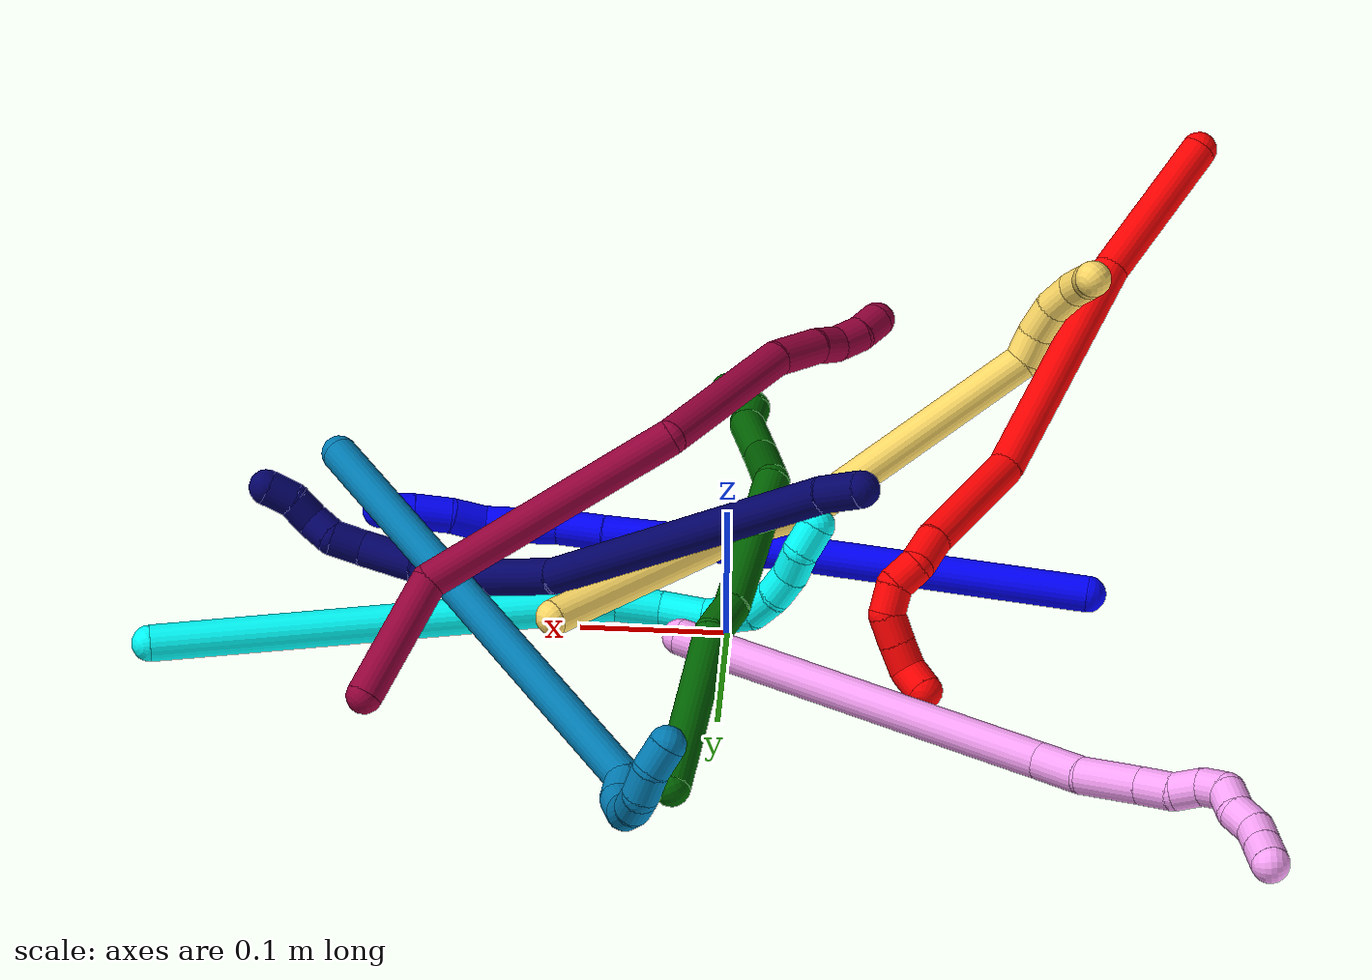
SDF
<sdf version="1.7">
 <world name="default">
  <plugin name="TubeGeneratorPlugin" filename="libtube_generator_plugin.so"/>
  <model name="photoneo_s_sensor">
   <static>1</static>
   <pose>0 0 2 1.57079 1.57079 3.14159</pose>
   <link name="link">
    <inertial><mass>0.1</mass></inertial>
    <sensor name="sensor" type="depth">
     <update_rate>30</update_rate>
     <camera>
      <horizontal_fov>1.22</horizontal_fov>
      <image><width>1920</width><height>1200</height><format>B8G8R8</format></image>
      <clip><near>0.1</near><far>4</far></clip>
      <depth_camera><output>points</output></depth_camera>
     </camera>
     <plugin name="camera_plugin" filename="libgazebo_ros_depth_camera.so">
      <baseline>0.2</baseline>
      <alwaysOn>1</alwaysOn>
      <updateRate>0.0</updateRate>
      <cameraName>camera_ir</cameraName>
      <imageTopicName>/camera/color/image_raw</imageTopicName>
      <cameraInfoTopicName>/camera/color/camera_info</cameraInfoTopicName>
      <depthImageTopicName>/camera/depth/image_raw</depthImageTopicName>
      <depthImageCameraInfoTopicName>/camera/depth/camera_info</depthImageCameraInfoTopicName>
      <pointCloudTopicName>/camera/depth/points</pointCloudTopicName>
      <frameName>fr_optical</frameName>
      <pointCloudCutoff>0.1</pointCloudCutoff>
      <pointCloudCutoffMax>2.0</pointCloudCutoffMax>
      <distortionK1>0</distortionK1>
      <distortionK2>0</distortionK2>
      <distortionK3>0</distortionK3>
      <distortionT1>0</distortionT1>
      <distortionT2>0</distortionT2>
      <CxPrime>0</CxPrime>
      <Cx>0</Cx>
      <Cy>0</Cy>
      <focalLength>0</focalLength>
      <hackBaseline>0</hackBaseline>
     </plugin>
    </sensor>
   </link>
  </model>
  <gravity>0 0 -9.8</gravity>
  <magnetic_field>6e-06 2.3e-05 -4.2e-05</magnetic_field>
  <atmosphere type="adiabatic"/>
  <physics name="default_physics" default="0" type="ode">
   <max_step_size>0.003</max_step_size>
   <real_time_factor>1</real_time_factor>
   <real_time_update_rate>1000</real_time_update_rate>
   <max_contacts>10000</max_contacts>
   <ode>
    <solver>
     <type>quick</type>
     <iters>100</iters>
     <sor>1.3</sor>
     <use_dynamic_moi_rescaling>0</use_dynamic_moi_rescaling>
    </solver>
    <constraints>
     <contact_max_correcting_vel>0</contact_max_correcting_vel>
     <contact_surface_layer>0.001</contact_surface_layer>
     <cfm>0</cfm>
     <erp>0.2</erp>
    </constraints>
   </ode>
  </physics>
  <scene><ambient>0.4 0.4 0.4 1</ambient><background>0.7 0.7 0.7 1</background><shadows>0</shadows></scene>
  <audio><device>default</device></audio>
  <spherical_coordinates>
   <surface_model>EARTH_WGS84</surface_model>
   <latitude_deg>0</latitude_deg>
   <longitude_deg>0</longitude_deg>
   <elevation>0</elevation>
   <heading_deg>0</heading_deg>
  </spherical_coordinates>
  <model name="bin">
   <static>1</static>
   <link name="bottom">
    <collision name="collision-bottom">
     <pose>0 0 -0.01 0 -0 0</pose>
     <geometry><box><size>0.8 0.6 0.02</size></box></geometry>
     <surface>
      <friction><ode><mu>100</mu><mu2>100</mu2></ode></friction>
      <contact><collide_bitmask>65535</collide_bitmask></contact>
     </surface>
    </collision>
   </link>
   <link name="west_wall">
    <collision name="collision-west_wall">
     <pose>-0.41 0 0.1 0 -0 0</pose>
     <geometry><box><size>0.02 0.6 0.2</size></box></geometry>
     <surface>
      <friction><ode><mu>100</mu><mu2>100</mu2></ode></friction>
      <contact><collide_bitmask>65535</collide_bitmask></contact>
     </surface>
    </collision>
   </link>
   <link name="east_wall">
    <collision name="collision-east_wall">
     <pose>0.41 0 0.1 0 -0 0</pose>
     <geometry><box><size>0.02 0.6 0.2</size></box></geometry>
     <surface>
      <friction><ode><mu>100</mu><mu2>100</mu2></ode></friction>
      <contact><collide_bitmask>65535</collide_bitmask></contact>
     </surface>
    </collision>
   </link>
   <link name="south_wall">
    <collision name="collision-south_wall">
     <pose>0 -0.31 0.1 0 -0 0</pose>
     <geometry><box><size>0.8 0.02 0.2</size></box></geometry>
     <surface>
      <friction><ode><mu>100</mu><mu2>100</mu2></ode></friction>
      <contact><collide_bitmask>65535</collide_bitmask></contact>
     </surface>
    </collision>
   </link>
   <link name="north_wall">
    <collision name="collision-north_wall">
     <pose>0 0.31 0.1 0 -0 0</pose>
     <geometry><box><size>0.8 0.02 0.2</size></box></geometry>
     <surface>
      <friction><ode><mu>100</mu><mu2>100</mu2></ode></friction>
      <contact><collide_bitmask>65535</collide_bitmask></contact>
     </surface>
    </collision>
   </link>
  </model>
  <model name="1">
   <static>0</static>
   <link name="1">
    <collision name="collision-cylinder-e_1_1_4">
     <pose>0.097182 -0.009251 -0.01038 2.41361 1.42869 2.31366</pose>
     <geometry><cylinder><radius>0.0125</radius><length>0.196344</length></cylinder></geometry>
     <surface>
      <friction><ode><mu>1.16</mu><mu2>1.16</mu2><slip1>0</slip1><slip2>0</slip2></ode></friction>
      <contact><ode><kp>1e+06</kp><kd>1</kd><max_vel>0</max_vel><min_depth>0.001</min_depth></ode></contact>
     </surface>
    </collision>
    <visual name="visual-cylinder-e_1_1_4">
     <pose>0.097182 -0.009251 -0.01038 2.41361 1.42869 2.31366</pose>
     <geometry><cylinder><radius>0.0125</radius><length>0.196344</length></cylinder></geometry>
     <material><ambient>0 0 1 1</ambient></material>
    </visual>
    <collision name="collision-cylinder-e_2_4_5">
     <pose>0.264811 -0.026251 -0.030454 2.46732 1.39642 2.35031</pose>
     <geometry><cylinder><radius>0.0125</radius><length>0.143063</length></cylinder></geometry>
     <surface>
      <friction><ode><mu>1.16</mu><mu2>1.16</mu2><slip1>0</slip1><slip2>0</slip2></ode></friction>
      <contact><ode><kp>1e+06</kp><kd>1</kd><max_vel>0</max_vel><min_depth>0.001</min_depth></ode></contact>
     </surface>
    </collision>
    <visual name="visual-cylinder-e_2_4_5">
     <pose>0.264811 -0.026251 -0.030454 2.46732 1.39642 2.35031</pose>
     <geometry><cylinder><radius>0.0125</radius><length>0.143063</length></cylinder></geometry>
     <material><ambient>0 0 1 1</ambient></material>
    </visual>
    <collision name="collision-cylinder-e_3_5_6">
     <pose>0.351437 -0.036861 -0.041654 2.05508 1.37352 1.87197</pose>
     <geometry><cylinder><radius>0.0125</radius><length>0.032998</length></cylinder></geometry>
     <surface>
      <friction><ode><mu>1.16</mu><mu2>1.16</mu2><slip1>0</slip1><slip2>0</slip2></ode></friction>
      <contact><ode><kp>1e+06</kp><kd>1</kd><max_vel>0</max_vel><min_depth>0.001</min_depth></ode></contact>
     </surface>
    </collision>
    <visual name="visual-cylinder-e_3_5_6">
     <pose>0.351437 -0.036861 -0.041654 2.05508 1.37352 1.87197</pose>
     <geometry><cylinder><radius>0.0125</radius><length>0.032998</length></cylinder></geometry>
     <material><ambient>0 0 1 1</ambient></material>
    </visual>
    <collision name="collision-cylinder-e_4_6_7">
     <pose>0.381856 -0.041549 -0.046142 2.59228 1.33001 2.45166</pose>
     <geometry><cylinder><radius>0.0125</radius><length>0.029324</length></cylinder></geometry>
     <surface>
      <friction><ode><mu>1.16</mu><mu2>1.16</mu2><slip1>0</slip1><slip2>0</slip2></ode></friction>
      <contact><ode><kp>1e+06</kp><kd>1</kd><max_vel>0</max_vel><min_depth>0.001</min_depth></ode></contact>
     </surface>
    </collision>
    <visual name="visual-cylinder-e_4_6_7">
     <pose>0.381856 -0.041549 -0.046142 2.59228 1.33001 2.45166</pose>
     <geometry><cylinder><radius>0.0125</radius><length>0.029324</length></cylinder></geometry>
     <material><ambient>0 0 1 1</ambient></material>
    </visual>
    <collision name="collision-cylinder-e_5_7_8">
     <pose>0.407766 -0.044249 -0.051475 2.78546 1.35911 2.70324</pose>
     <geometry><cylinder><radius>0.0125</radius><length>0.023875</length></cylinder></geometry>
     <surface>
      <friction><ode><mu>1.16</mu><mu2>1.16</mu2><slip1>0</slip1><slip2>0</slip2></ode></friction>
      <contact><ode><kp>1e+06</kp><kd>1</kd><max_vel>0</max_vel><min_depth>0.001</min_depth></ode></contact>
     </surface>
    </collision>
    <visual name="visual-cylinder-e_5_7_8">
     <pose>0.407766 -0.044249 -0.051475 2.78546 1.35911 2.70324</pose>
     <geometry><cylinder><radius>0.0125</radius><length>0.023875</length></cylinder></geometry>
     <material><ambient>0 0 1 1</ambient></material>
    </visual>
    <collision name="collision-cylinder-e_6_8_9">
     <pose>0.430803 -0.040374 -0.055229 -1.85814 1.15986 -1.43954</pose>
     <geometry><cylinder><radius>0.0125</radius><length>0.024796</length></cylinder></geometry>
     <surface>
      <friction><ode><mu>1.16</mu><mu2>1.16</mu2><slip1>0</slip1><slip2>0</slip2></ode></friction>
      <contact><ode><kp>1e+06</kp><kd>1</kd><max_vel>0</max_vel><min_depth>0.001</min_depth></ode></contact>
     </surface>
    </collision>
    <visual name="visual-cylinder-e_6_8_9">
     <pose>0.430803 -0.040374 -0.055229 -1.85814 1.15986 -1.43954</pose>
     <geometry><cylinder><radius>0.0125</radius><length>0.024796</length></cylinder></geometry>
     <material><ambient>0 0 1 1</ambient></material>
    </visual>
    <collision name="collision-cylinder-e_7_9_10">
     <pose>0.454956 -0.033658 -0.059045 -2.4578 1.33211 -2.29115</pose>
     <geometry><cylinder><radius>0.0125</radius><length>0.026321</length></cylinder></geometry>
     <surface>
      <friction><ode><mu>1.16</mu><mu2>1.16</mu2><slip1>0</slip1><slip2>0</slip2></ode></friction>
      <contact><ode><kp>1e+06</kp><kd>1</kd><max_vel>0</max_vel><min_depth>0.001</min_depth></ode></contact>
     </surface>
    </collision>
    <visual name="visual-cylinder-e_7_9_10">
     <pose>0.454956 -0.033658 -0.059045 -2.4578 1.33211 -2.29115</pose>
     <geometry><cylinder><radius>0.0125</radius><length>0.026321</length></cylinder></geometry>
     <material><ambient>0 0 1 1</ambient></material>
    </visual>
    <collision name="collision-cylinder-e_8_10_2">
     <pose>0.478834 -0.029885 -0.064489 -2.60405 1.26263 -2.42103</pose>
     <geometry><cylinder><radius>0.0125</radius><length>0.023278</length></cylinder></geometry>
     <surface>
      <friction><ode><mu>1.16</mu><mu2>1.16</mu2><slip1>0</slip1><slip2>0</slip2></ode></friction>
      <contact><ode><kp>1e+06</kp><kd>1</kd><max_vel>0</max_vel><min_depth>0.001</min_depth></ode></contact>
     </surface>
    </collision>
    <visual name="visual-cylinder-e_8_10_2">
     <pose>0.478834 -0.029885 -0.064489 -2.60405 1.26263 -2.42103</pose>
     <geometry><cylinder><radius>0.0125</radius><length>0.023278</length></cylinder></geometry>
     <material><ambient>0 0 1 1</ambient></material>
    </visual>
    <collision name="collision-sphere-2">
     <pose>0.489925 -0.028078 -0.067521 0 -0 0</pose>
     <geometry><sphere><radius>0.0125</radius></sphere></geometry>
     <surface>
      <friction><ode><mu>1.16</mu><mu2>1.16</mu2><slip1>0</slip1><slip2>0</slip2></ode></friction>
      <contact><ode><kp>1e+06</kp><kd>1</kd><max_vel>0</max_vel><min_depth>0.001</min_depth></ode></contact>
     </surface>
    </collision>
    <visual name="visual-sphere-2">
     <pose>0.489925 -0.028078 -0.067521 0 -0 0</pose>
     <geometry><sphere><radius>0.0125</radius></sphere></geometry>
     <material><ambient>0 0 1 1</ambient></material>
    </visual>
    <collision name="collision-sphere-10">
     <pose>0.467744 -0.031693 -0.061457 0 -0 0</pose>
     <geometry><sphere><radius>0.0125</radius></sphere></geometry>
     <surface>
      <friction><ode><mu>1.16</mu><mu2>1.16</mu2><slip1>0</slip1><slip2>0</slip2></ode></friction>
      <contact><ode><kp>1e+06</kp><kd>1</kd><max_vel>0</max_vel><min_depth>0.001</min_depth></ode></contact>
     </surface>
    </collision>
    <visual name="visual-sphere-10">
     <pose>0.467744 -0.031693 -0.061457 0 -0 0</pose>
     <geometry><sphere><radius>0.0125</radius></sphere></geometry>
     <material><ambient>0 0 1 1</ambient></material>
    </visual>
    <collision name="collision-sphere-9">
     <pose>0.442169 -0.035624 -0.056633 0 -0 0</pose>
     <geometry><sphere><radius>0.0125</radius></sphere></geometry>
     <surface>
      <friction><ode><mu>1.16</mu><mu2>1.16</mu2><slip1>0</slip1><slip2>0</slip2></ode></friction>
      <contact><ode><kp>1e+06</kp><kd>1</kd><max_vel>0</max_vel><min_depth>0.001</min_depth></ode></contact>
     </surface>
    </collision>
    <visual name="visual-sphere-9">
     <pose>0.442169 -0.035624 -0.056633 0 -0 0</pose>
     <geometry><sphere><radius>0.0125</radius></sphere></geometry>
     <material><ambient>0 0 1 1</ambient></material>
    </visual>
    <collision name="collision-sphere-4">
     <pose>0.194365 -0.018503 -0.020759 0 -0 0</pose>
     <geometry><sphere><radius>0.0125</radius></sphere></geometry>
     <surface>
      <friction><ode><mu>1.16</mu><mu2>1.16</mu2><slip1>0</slip1><slip2>0</slip2></ode></friction>
      <contact><ode><kp>1e+06</kp><kd>1</kd><max_vel>0</max_vel><min_depth>0.001</min_depth></ode></contact>
     </surface>
    </collision>
    <visual name="visual-sphere-4">
     <pose>0.194365 -0.018503 -0.020759 0 -0 0</pose>
     <geometry><sphere><radius>0.0125</radius></sphere></geometry>
     <material><ambient>0 0 1 1</ambient></material>
    </visual>
    <collision name="collision-sphere-1">
     <geometry><sphere><radius>0.0125</radius></sphere></geometry>
     <surface>
      <friction><ode><mu>1.16</mu><mu2>1.16</mu2><slip1>0</slip1><slip2>0</slip2></ode></friction>
      <contact><ode><kp>1e+06</kp><kd>1</kd><max_vel>0</max_vel><min_depth>0.001</min_depth></ode></contact>
     </surface>
    </collision>
    <visual name="visual-sphere-1">
     <geometry><sphere><radius>0.0125</radius></sphere></geometry>
     <material><ambient>0 0 1 1</ambient></material>
    </visual>
    <collision name="collision-sphere-8">
     <pose>0.419437 -0.045123 -0.053825 0 -0 0</pose>
     <geometry><sphere><radius>0.0125</radius></sphere></geometry>
     <surface>
      <friction><ode><mu>1.16</mu><mu2>1.16</mu2><slip1>0</slip1><slip2>0</slip2></ode></friction>
      <contact><ode><kp>1e+06</kp><kd>1</kd><max_vel>0</max_vel><min_depth>0.001</min_depth></ode></contact>
     </surface>
    </collision>
    <visual name="visual-sphere-8">
     <pose>0.419437 -0.045123 -0.053825 0 -0 0</pose>
     <geometry><sphere><radius>0.0125</radius></sphere></geometry>
     <material><ambient>0 0 1 1</ambient></material>
    </visual>
    <collision name="collision-sphere-5">
     <pose>0.335258 -0.033999 -0.040148 0 -0 0</pose>
     <geometry><sphere><radius>0.0125</radius></sphere></geometry>
     <surface>
      <friction><ode><mu>1.16</mu><mu2>1.16</mu2><slip1>0</slip1><slip2>0</slip2></ode></friction>
      <contact><ode><kp>1e+06</kp><kd>1</kd><max_vel>0</max_vel><min_depth>0.001</min_depth></ode></contact>
     </surface>
    </collision>
    <visual name="visual-sphere-5">
     <pose>0.335258 -0.033999 -0.040148 0 -0 0</pose>
     <geometry><sphere><radius>0.0125</radius></sphere></geometry>
     <material><ambient>0 0 1 1</ambient></material>
    </visual>
    <collision name="collision-sphere-6">
     <pose>0.367617 -0.039723 -0.04316 0 -0 0</pose>
     <geometry><sphere><radius>0.0125</radius></sphere></geometry>
     <surface>
      <friction><ode><mu>1.16</mu><mu2>1.16</mu2><slip1>0</slip1><slip2>0</slip2></ode></friction>
      <contact><ode><kp>1e+06</kp><kd>1</kd><max_vel>0</max_vel><min_depth>0.001</min_depth></ode></contact>
     </surface>
    </collision>
    <visual name="visual-sphere-6">
     <pose>0.367617 -0.039723 -0.04316 0 -0 0</pose>
     <geometry><sphere><radius>0.0125</radius></sphere></geometry>
     <material><ambient>0 0 1 1</ambient></material>
    </visual>
    <collision name="collision-sphere-7">
     <pose>0.396095 -0.043374 -0.049124 0 -0 0</pose>
     <geometry><sphere><radius>0.0125</radius></sphere></geometry>
     <surface>
      <friction><ode><mu>1.16</mu><mu2>1.16</mu2><slip1>0</slip1><slip2>0</slip2></ode></friction>
      <contact><ode><kp>1e+06</kp><kd>1</kd><max_vel>0</max_vel><min_depth>0.001</min_depth></ode></contact>
     </surface>
    </collision>
    <visual name="visual-sphere-7">
     <pose>0.396095 -0.043374 -0.049124 0 -0 0</pose>
     <geometry><sphere><radius>0.0125</radius></sphere></geometry>
     <material><ambient>0 0 1 1</ambient></material>
    </visual>
    <inertial>
     <pose>0.246599 -0.023292 -0.029552 0 -0 0</pose>
     <mass>0.5</mass>
     <inertia>
      <ixx>4.2e-05</ixx>
      <ixy>0</ixy>
      <ixz>0</ixz>
      <iyy>0.000989</iyy>
      <iyz>0</iyz>
      <izz>-0.000812</izz>
     </inertia>
    </inertial>
   </link>
   <pose>-0.244762 -0.054586 0.00603 0.863217 -0.163687 -0.157312</pose>
  </model>
  <model name="2">
   <static>0</static>
   <link name="2">
    <collision name="collision-cylinder-e_1_1_4">
     <pose>-0.015899 0.031822 -0.043032 -2.50485 -0.28877 0.83095</pose>
     <geometry><cylinder><radius>0.0125</radius><length>0.111663</length></cylinder></geometry>
     <surface>
      <friction><ode><mu>1.16</mu><mu2>1.16</mu2><slip1>0</slip1><slip2>0</slip2></ode></friction>
      <contact><ode><kp>1e+06</kp><kd>1</kd><max_vel>0</max_vel><min_depth>0.001</min_depth></ode></contact>
     </surface>
    </collision>
    <visual name="visual-cylinder-e_1_1_4">
     <pose>-0.015899 0.031822 -0.043032 -2.50485 -0.28877 0.83095</pose>
     <geometry><cylinder><radius>0.0125</radius><length>0.111663</length></cylinder></geometry>
     <material><ambient>1 0 0 1</ambient></material>
    </visual>
    <collision name="collision-cylinder-e_2_4_5">
     <pose>-0.044808 0.105408 -0.162466 -2.64133 -0.148308 0.565967</pose>
     <geometry><cylinder><radius>0.0125</radius><length>0.176078</length></cylinder></geometry>
     <surface>
      <friction><ode><mu>1.16</mu><mu2>1.16</mu2><slip1>0</slip1><slip2>0</slip2></ode></friction>
      <contact><ode><kp>1e+06</kp><kd>1</kd><max_vel>0</max_vel><min_depth>0.001</min_depth></ode></contact>
     </surface>
    </collision>
    <visual name="visual-cylinder-e_2_4_5">
     <pose>-0.044808 0.105408 -0.162466 -2.64133 -0.148308 0.565967</pose>
     <geometry><cylinder><radius>0.0125</radius><length>0.176078</length></cylinder></geometry>
     <material><ambient>1 0 0 1</ambient></material>
    </visual>
    <collision name="collision-cylinder-e_3_5_6">
     <pose>-0.073489 0.158426 -0.277221 -2.85618 -0.373685 1.84181</pose>
     <geometry><cylinder><radius>0.0125</radius><length>0.085863</length></cylinder></geometry>
     <surface>
      <friction><ode><mu>1.16</mu><mu2>1.16</mu2><slip1>0</slip1><slip2>0</slip2></ode></friction>
      <contact><ode><kp>1e+06</kp><kd>1</kd><max_vel>0</max_vel><min_depth>0.001</min_depth></ode></contact>
     </surface>
    </collision>
    <visual name="visual-cylinder-e_3_5_6">
     <pose>-0.073489 0.158426 -0.277221 -2.85618 -0.373685 1.84181</pose>
     <geometry><cylinder><radius>0.0125</radius><length>0.085863</length></cylinder></geometry>
     <material><ambient>1 0 0 1</ambient></material>
    </visual>
    <collision name="collision-cylinder-e_4_6_7">
     <pose>-0.091852 0.173676 -0.32744 -2.81671 -0.211665 1.15022</pose>
     <geometry><cylinder><radius>0.0125</radius><length>0.025616</length></cylinder></geometry>
     <surface>
      <friction><ode><mu>1.16</mu><mu2>1.16</mu2><slip1>0</slip1><slip2>0</slip2></ode></friction>
      <contact><ode><kp>1e+06</kp><kd>1</kd><max_vel>0</max_vel><min_depth>0.001</min_depth></ode></contact>
     </surface>
    </collision>
    <visual name="visual-cylinder-e_4_6_7">
     <pose>-0.091852 0.173676 -0.32744 -2.81671 -0.211665 1.15022</pose>
     <geometry><cylinder><radius>0.0125</radius><length>0.025616</length></cylinder></geometry>
     <material><ambient>1 0 0 1</ambient></material>
    </visual>
    <collision name="collision-cylinder-e_5_7_8">
     <pose>-0.09939 0.184229 -0.345269 -2.30882 -0.50058 1.04828</pose>
     <geometry><cylinder><radius>0.0125</radius><length>0.020201</length></cylinder></geometry>
     <surface>
      <friction><ode><mu>1.16</mu><mu2>1.16</mu2><slip1>0</slip1><slip2>0</slip2></ode></friction>
      <contact><ode><kp>1e+06</kp><kd>1</kd><max_vel>0</max_vel><min_depth>0.001</min_depth></ode></contact>
     </surface>
    </collision>
    <visual name="visual-cylinder-e_5_7_8">
     <pose>-0.09939 0.184229 -0.345269 -2.30882 -0.50058 1.04828</pose>
     <geometry><cylinder><radius>0.0125</radius><length>0.020201</length></cylinder></geometry>
     <material><ambient>1 0 0 1</ambient></material>
    </visual>
    <collision name="collision-cylinder-e_6_8_9">
     <pose>-0.103361 0.199031 -0.357209 -2.19801 0.08593 -0.168124</pose>
     <geometry><cylinder><radius>0.0125</radius><length>0.020446</length></cylinder></geometry>
     <surface>
      <friction><ode><mu>1.16</mu><mu2>1.16</mu2><slip1>0</slip1><slip2>0</slip2></ode></friction>
      <contact><ode><kp>1e+06</kp><kd>1</kd><max_vel>0</max_vel><min_depth>0.001</min_depth></ode></contact>
     </surface>
    </collision>
    <visual name="visual-cylinder-e_6_8_9">
     <pose>-0.103361 0.199031 -0.357209 -2.19801 0.08593 -0.168124</pose>
     <geometry><cylinder><radius>0.0125</radius><length>0.020446</length></cylinder></geometry>
     <material><ambient>1 0 0 1</ambient></material>
    </visual>
    <collision name="collision-cylinder-e_7_9_10">
     <pose>-0.096163 0.214382 -0.366474 -2.00421 0.679187 -1.00991</pose>
     <geometry><cylinder><radius>0.0125</radius><length>0.020123</length></cylinder></geometry>
     <surface>
      <friction><ode><mu>1.16</mu><mu2>1.16</mu2><slip1>0</slip1><slip2>0</slip2></ode></friction>
      <contact><ode><kp>1e+06</kp><kd>1</kd><max_vel>0</max_vel><min_depth>0.001</min_depth></ode></contact>
     </surface>
    </collision>
    <visual name="visual-cylinder-e_7_9_10">
     <pose>-0.096163 0.214382 -0.366474 -2.00421 0.679187 -1.00991</pose>
     <geometry><cylinder><radius>0.0125</radius><length>0.020123</length></cylinder></geometry>
     <material><ambient>1 0 0 1</ambient></material>
    </visual>
    <collision name="collision-cylinder-e_8_10_11">
     <pose>-0.083253 0.228163 -0.373241 -2.05119 0.719032 -1.10953</pose>
     <geometry><cylinder><radius>0.0125</radius><length>0.020009</length></cylinder></geometry>
     <surface>
      <friction><ode><mu>1.16</mu><mu2>1.16</mu2><slip1>0</slip1><slip2>0</slip2></ode></friction>
      <contact><ode><kp>1e+06</kp><kd>1</kd><max_vel>0</max_vel><min_depth>0.001</min_depth></ode></contact>
     </surface>
    </collision>
    <visual name="visual-cylinder-e_8_10_11">
     <pose>-0.083253 0.228163 -0.373241 -2.05119 0.719032 -1.10953</pose>
     <geometry><cylinder><radius>0.0125</radius><length>0.020009</length></cylinder></geometry>
     <material><ambient>1 0 0 1</ambient></material>
    </visual>
    <collision name="collision-cylinder-e_9_11_2">
     <pose>-0.069362 0.23584 -0.38348 -2.99461 0.818442 -2.80529</pose>
     <geometry><cylinder><radius>0.0125</radius><length>0.02</length></cylinder></geometry>
     <surface>
      <friction><ode><mu>1.16</mu><mu2>1.16</mu2><slip1>0</slip1><slip2>0</slip2></ode></friction>
      <contact><ode><kp>1e+06</kp><kd>1</kd><max_vel>0</max_vel><min_depth>0.001</min_depth></ode></contact>
     </surface>
    </collision>
    <visual name="visual-cylinder-e_9_11_2">
     <pose>-0.069362 0.23584 -0.38348 -2.99461 0.818442 -2.80529</pose>
     <geometry><cylinder><radius>0.0125</radius><length>0.02</length></cylinder></geometry>
     <material><ambient>1 0 0 1</ambient></material>
    </visual>
    <collision name="collision-sphere-2">
     <pose>-0.062061 0.236841 -0.39024 0 -0 0</pose>
     <geometry><sphere><radius>0.0125</radius></sphere></geometry>
     <surface>
      <friction><ode><mu>1.16</mu><mu2>1.16</mu2><slip1>0</slip1><slip2>0</slip2></ode></friction>
      <contact><ode><kp>1e+06</kp><kd>1</kd><max_vel>0</max_vel><min_depth>0.001</min_depth></ode></contact>
     </surface>
    </collision>
    <visual name="visual-sphere-2">
     <pose>-0.062061 0.236841 -0.39024 0 -0 0</pose>
     <geometry><sphere><radius>0.0125</radius></sphere></geometry>
     <material><ambient>1 0 0 1</ambient></material>
    </visual>
    <collision name="collision-sphere-11">
     <pose>-0.076663 0.234839 -0.37672 0 -0 0</pose>
     <geometry><sphere><radius>0.0125</radius></sphere></geometry>
     <surface>
      <friction><ode><mu>1.16</mu><mu2>1.16</mu2><slip1>0</slip1><slip2>0</slip2></ode></friction>
      <contact><ode><kp>1e+06</kp><kd>1</kd><max_vel>0</max_vel><min_depth>0.001</min_depth></ode></contact>
     </surface>
    </collision>
    <visual name="visual-sphere-11">
     <pose>-0.076663 0.234839 -0.37672 0 -0 0</pose>
     <geometry><sphere><radius>0.0125</radius></sphere></geometry>
     <material><ambient>1 0 0 1</ambient></material>
    </visual>
    <collision name="collision-sphere-10">
     <pose>-0.089843 0.221487 -0.369762 0 -0 0</pose>
     <geometry><sphere><radius>0.0125</radius></sphere></geometry>
     <surface>
      <friction><ode><mu>1.16</mu><mu2>1.16</mu2><slip1>0</slip1><slip2>0</slip2></ode></friction>
      <contact><ode><kp>1e+06</kp><kd>1</kd><max_vel>0</max_vel><min_depth>0.001</min_depth></ode></contact>
     </surface>
    </collision>
    <visual name="visual-sphere-10">
     <pose>-0.089843 0.221487 -0.369762 0 -0 0</pose>
     <geometry><sphere><radius>0.0125</radius></sphere></geometry>
     <material><ambient>1 0 0 1</ambient></material>
    </visual>
    <collision name="collision-sphere-9">
     <pose>-0.102483 0.207277 -0.363186 0 -0 0</pose>
     <geometry><sphere><radius>0.0125</radius></sphere></geometry>
     <surface>
      <friction><ode><mu>1.16</mu><mu2>1.16</mu2><slip1>0</slip1><slip2>0</slip2></ode></friction>
      <contact><ode><kp>1e+06</kp><kd>1</kd><max_vel>0</max_vel><min_depth>0.001</min_depth></ode></contact>
     </surface>
    </collision>
    <visual name="visual-sphere-9">
     <pose>-0.102483 0.207277 -0.363186 0 -0 0</pose>
     <geometry><sphere><radius>0.0125</radius></sphere></geometry>
     <material><ambient>1 0 0 1</ambient></material>
    </visual>
    <collision name="collision-sphere-4">
     <pose>-0.031799 0.063643 -0.086064 0 -0 0</pose>
     <geometry><sphere><radius>0.0125</radius></sphere></geometry>
     <surface>
      <friction><ode><mu>1.16</mu><mu2>1.16</mu2><slip1>0</slip1><slip2>0</slip2></ode></friction>
      <contact><ode><kp>1e+06</kp><kd>1</kd><max_vel>0</max_vel><min_depth>0.001</min_depth></ode></contact>
     </surface>
    </collision>
    <visual name="visual-sphere-4">
     <pose>-0.031799 0.063643 -0.086064 0 -0 0</pose>
     <geometry><sphere><radius>0.0125</radius></sphere></geometry>
     <material><ambient>1 0 0 1</ambient></material>
    </visual>
    <collision name="collision-sphere-1">
     <geometry><sphere><radius>0.0125</radius></sphere></geometry>
     <surface>
      <friction><ode><mu>1.16</mu><mu2>1.16</mu2><slip1>0</slip1><slip2>0</slip2></ode></friction>
      <contact><ode><kp>1e+06</kp><kd>1</kd><max_vel>0</max_vel><min_depth>0.001</min_depth></ode></contact>
     </surface>
    </collision>
    <visual name="visual-sphere-1">
     <geometry><sphere><radius>0.0125</radius></sphere></geometry>
     <material><ambient>1 0 0 1</ambient></material>
    </visual>
    <collision name="collision-sphere-8">
     <pose>-0.104238 0.190784 -0.351231 0 -0 0</pose>
     <geometry><sphere><radius>0.0125</radius></sphere></geometry>
     <surface>
      <friction><ode><mu>1.16</mu><mu2>1.16</mu2><slip1>0</slip1><slip2>0</slip2></ode></friction>
      <contact><ode><kp>1e+06</kp><kd>1</kd><max_vel>0</max_vel><min_depth>0.001</min_depth></ode></contact>
     </surface>
    </collision>
    <visual name="visual-sphere-8">
     <pose>-0.104238 0.190784 -0.351231 0 -0 0</pose>
     <geometry><sphere><radius>0.0125</radius></sphere></geometry>
     <material><ambient>1 0 0 1</ambient></material>
    </visual>
    <collision name="collision-sphere-5">
     <pose>-0.057817 0.147172 -0.238868 0 -0 0</pose>
     <geometry><sphere><radius>0.0125</radius></sphere></geometry>
     <surface>
      <friction><ode><mu>1.16</mu><mu2>1.16</mu2><slip1>0</slip1><slip2>0</slip2></ode></friction>
      <contact><ode><kp>1e+06</kp><kd>1</kd><max_vel>0</max_vel><min_depth>0.001</min_depth></ode></contact>
     </surface>
    </collision>
    <visual name="visual-sphere-5">
     <pose>-0.057817 0.147172 -0.238868 0 -0 0</pose>
     <geometry><sphere><radius>0.0125</radius></sphere></geometry>
     <material><ambient>1 0 0 1</ambient></material>
    </visual>
    <collision name="collision-sphere-6">
     <pose>-0.089161 0.169679 -0.315573 0 -0 0</pose>
     <geometry><sphere><radius>0.0125</radius></sphere></geometry>
     <surface>
      <friction><ode><mu>1.16</mu><mu2>1.16</mu2><slip1>0</slip1><slip2>0</slip2></ode></friction>
      <contact><ode><kp>1e+06</kp><kd>1</kd><max_vel>0</max_vel><min_depth>0.001</min_depth></ode></contact>
     </surface>
    </collision>
    <visual name="visual-sphere-6">
     <pose>-0.089161 0.169679 -0.315573 0 -0 0</pose>
     <geometry><sphere><radius>0.0125</radius></sphere></geometry>
     <material><ambient>1 0 0 1</ambient></material>
    </visual>
    <collision name="collision-sphere-7">
     <pose>-0.094543 0.177673 -0.339307 0 -0 0</pose>
     <geometry><sphere><radius>0.0125</radius></sphere></geometry>
     <surface>
      <friction><ode><mu>1.16</mu><mu2>1.16</mu2><slip1>0</slip1><slip2>0</slip2></ode></friction>
      <contact><ode><kp>1e+06</kp><kd>1</kd><max_vel>0</max_vel><min_depth>0.001</min_depth></ode></contact>
     </surface>
    </collision>
    <visual name="visual-sphere-7">
     <pose>-0.094543 0.177673 -0.339307 0 -0 0</pose>
     <geometry><sphere><radius>0.0125</radius></sphere></geometry>
     <material><ambient>1 0 0 1</ambient></material>
    </visual>
    <inertial>
     <pose>-0.054874 0.123105 -0.204787 0 -0 0</pose>
     <mass>0.5</mass>
     <inertia>
      <ixx>0.000829</ixx>
      <ixy>0</ixy>
      <ixz>0</ixz>
      <iyy>4.6e-05</iyy>
      <iyz>0</iyz>
      <izz>-0.000217</izz>
     </inertia>
    </inertial>
   </link>
   <pose>-0.311716 -0.302491 0.215389 -1.59005 0.276244 3.00374</pose>
  </model>
  <model name="3">
   <static>0</static>
   <link name="3">
    <collision name="collision-cylinder-e_1_1_4">
     <pose>-0.087012 -0.00966 -0.131867 3.06846 -0.582036 -2.89854</pose>
     <geometry><cylinder><radius>0.0125</radius><length>0.316565</length></cylinder></geometry>
     <surface>
      <friction><ode><mu>1.16</mu><mu2>1.16</mu2><slip1>0</slip1><slip2>0</slip2></ode></friction>
      <contact><ode><kp>1e+06</kp><kd>1</kd><max_vel>0</max_vel><min_depth>0.001</min_depth></ode></contact>
     </surface>
    </collision>
    <visual name="visual-cylinder-e_1_1_4">
     <pose>-0.087012 -0.00966 -0.131867 3.06846 -0.582036 -2.89854</pose>
     <geometry><cylinder><radius>0.0125</radius><length>0.316565</length></cylinder></geometry>
     <material><ambient>0.003922 1 0.996078 1</ambient></material>
    </visual>
    <collision name="collision-cylinder-e_2_4_5">
     <pose>-0.185604 -0.017443 -0.274987 -2.97619 -0.792832 2.7506</pose>
     <geometry><cylinder><radius>0.0125</radius><length>0.032511</length></cylinder></geometry>
     <surface>
      <friction><ode><mu>1.16</mu><mu2>1.16</mu2><slip1>0</slip1><slip2>0</slip2></ode></friction>
      <contact><ode><kp>1e+06</kp><kd>1</kd><max_vel>0</max_vel><min_depth>0.001</min_depth></ode></contact>
     </surface>
    </collision>
    <visual name="visual-cylinder-e_2_4_5">
     <pose>-0.185604 -0.017443 -0.274987 -2.97619 -0.792832 2.7506</pose>
     <geometry><cylinder><radius>0.0125</radius><length>0.032511</length></cylinder></geometry>
     <material><ambient>0.003922 1 0.996078 1</ambient></material>
    </visual>
    <collision name="collision-cylinder-e_3_5_6">
     <pose>-0.210818 -0.013632 -0.294518 -2.91229 -1.01332 2.73241</pose>
     <geometry><cylinder><radius>0.0125</radius><length>0.032135</length></cylinder></geometry>
     <surface>
      <friction><ode><mu>1.16</mu><mu2>1.16</mu2><slip1>0</slip1><slip2>0</slip2></ode></friction>
      <contact><ode><kp>1e+06</kp><kd>1</kd><max_vel>0</max_vel><min_depth>0.001</min_depth></ode></contact>
     </surface>
    </collision>
    <visual name="visual-cylinder-e_3_5_6">
     <pose>-0.210818 -0.013632 -0.294518 -2.91229 -1.01332 2.73241</pose>
     <geometry><cylinder><radius>0.0125</radius><length>0.032135</length></cylinder></geometry>
     <material><ambient>0.003922 1 0.996078 1</ambient></material>
    </visual>
    <collision name="collision-cylinder-e_4_6_7">
     <pose>-0.238617 -0.014403 -0.311241 2.83177 -1.01149 -2.59188</pose>
     <geometry><cylinder><radius>0.0125</radius><length>0.033422</length></cylinder></geometry>
     <surface>
      <friction><ode><mu>1.16</mu><mu2>1.16</mu2><slip1>0</slip1><slip2>0</slip2></ode></friction>
      <contact><ode><kp>1e+06</kp><kd>1</kd><max_vel>0</max_vel><min_depth>0.001</min_depth></ode></contact>
     </surface>
    </collision>
    <visual name="visual-cylinder-e_4_6_7">
     <pose>-0.238617 -0.014403 -0.311241 2.83177 -1.01149 -2.59188</pose>
     <geometry><cylinder><radius>0.0125</radius><length>0.033422</length></cylinder></geometry>
     <material><ambient>0.003922 1 0.996078 1</ambient></material>
    </visual>
    <collision name="collision-cylinder-e_5_7_8">
     <pose>-0.262054 -0.023876 -0.321156 1.78474 -0.929122 -1.11247</pose>
     <geometry><cylinder><radius>0.0125</radius><length>0.023148</length></cylinder></geometry>
     <surface>
      <friction><ode><mu>1.16</mu><mu2>1.16</mu2><slip1>0</slip1><slip2>0</slip2></ode></friction>
      <contact><ode><kp>1e+06</kp><kd>1</kd><max_vel>0</max_vel><min_depth>0.001</min_depth></ode></contact>
     </surface>
    </collision>
    <visual name="visual-cylinder-e_5_7_8">
     <pose>-0.262054 -0.023876 -0.321156 1.78474 -0.929122 -1.11247</pose>
     <geometry><cylinder><radius>0.0125</radius><length>0.023148</length></cylinder></geometry>
     <material><ambient>0.003922 1 0.996078 1</ambient></material>
    </visual>
    <collision name="collision-cylinder-e_6_8_9">
     <pose>-0.277465 -0.038439 -0.324636 1.82314 -0.651703 -0.82242</pose>
     <geometry><cylinder><radius>0.0125</radius><length>0.020244</length></cylinder></geometry>
     <surface>
      <friction><ode><mu>1.16</mu><mu2>1.16</mu2><slip1>0</slip1><slip2>0</slip2></ode></friction>
      <contact><ode><kp>1e+06</kp><kd>1</kd><max_vel>0</max_vel><min_depth>0.001</min_depth></ode></contact>
     </surface>
    </collision>
    <visual name="visual-cylinder-e_6_8_9">
     <pose>-0.277465 -0.038439 -0.324636 1.82314 -0.651703 -0.82242</pose>
     <geometry><cylinder><radius>0.0125</radius><length>0.020244</length></cylinder></geometry>
     <material><ambient>0.003922 1 0.996078 1</ambient></material>
    </visual>
    <collision name="collision-cylinder-e_7_9_10">
     <pose>-0.289471 -0.054807 -0.325971 1.49234 -0.598518 -0.555689</pose>
     <geometry><cylinder><radius>0.0125</radius><length>0.020824</length></cylinder></geometry>
     <surface>
      <friction><ode><mu>1.16</mu><mu2>1.16</mu2><slip1>0</slip1><slip2>0</slip2></ode></friction>
      <contact><ode><kp>1e+06</kp><kd>1</kd><max_vel>0</max_vel><min_depth>0.001</min_depth></ode></contact>
     </surface>
    </collision>
    <visual name="visual-cylinder-e_7_9_10">
     <pose>-0.289471 -0.054807 -0.325971 1.49234 -0.598518 -0.555689</pose>
     <geometry><cylinder><radius>0.0125</radius><length>0.020824</length></cylinder></geometry>
     <material><ambient>0.003922 1 0.996078 1</ambient></material>
    </visual>
    <collision name="collision-cylinder-e_8_10_2">
     <pose>-0.299076 -0.072463 -0.329222 1.97878 -0.361389 -0.542283</pose>
     <geometry><cylinder><radius>0.0125</radius><length>0.021151</length></cylinder></geometry>
     <surface>
      <friction><ode><mu>1.16</mu><mu2>1.16</mu2><slip1>0</slip1><slip2>0</slip2></ode></friction>
      <contact><ode><kp>1e+06</kp><kd>1</kd><max_vel>0</max_vel><min_depth>0.001</min_depth></ode></contact>
     </surface>
    </collision>
    <visual name="visual-cylinder-e_8_10_2">
     <pose>-0.299076 -0.072463 -0.329222 1.97878 -0.361389 -0.542283</pose>
     <geometry><cylinder><radius>0.0125</radius><length>0.021151</length></cylinder></geometry>
     <material><ambient>0.003922 1 0.996078 1</ambient></material>
    </visual>
    <collision name="collision-sphere-2">
     <pose>-0.302815 -0.081543 -0.333147 0 -0 0</pose>
     <geometry><sphere><radius>0.0125</radius></sphere></geometry>
     <surface>
      <friction><ode><mu>1.16</mu><mu2>1.16</mu2><slip1>0</slip1><slip2>0</slip2></ode></friction>
      <contact><ode><kp>1e+06</kp><kd>1</kd><max_vel>0</max_vel><min_depth>0.001</min_depth></ode></contact>
     </surface>
    </collision>
    <visual name="visual-sphere-2">
     <pose>-0.302815 -0.081543 -0.333147 0 -0 0</pose>
     <geometry><sphere><radius>0.0125</radius></sphere></geometry>
     <material><ambient>0.003922 1 0.996078 1</ambient></material>
    </visual>
    <collision name="collision-sphere-10">
     <pose>-0.295337 -0.063382 -0.325297 0 -0 0</pose>
     <geometry><sphere><radius>0.0125</radius></sphere></geometry>
     <surface>
      <friction><ode><mu>1.16</mu><mu2>1.16</mu2><slip1>0</slip1><slip2>0</slip2></ode></friction>
      <contact><ode><kp>1e+06</kp><kd>1</kd><max_vel>0</max_vel><min_depth>0.001</min_depth></ode></contact>
     </surface>
    </collision>
    <visual name="visual-sphere-10">
     <pose>-0.295337 -0.063382 -0.325297 0 -0 0</pose>
     <geometry><sphere><radius>0.0125</radius></sphere></geometry>
     <material><ambient>0.003922 1 0.996078 1</ambient></material>
    </visual>
    <collision name="collision-sphere-9">
     <pose>-0.283604 -0.046231 -0.326645 0 -0 0</pose>
     <geometry><sphere><radius>0.0125</radius></sphere></geometry>
     <surface>
      <friction><ode><mu>1.16</mu><mu2>1.16</mu2><slip1>0</slip1><slip2>0</slip2></ode></friction>
      <contact><ode><kp>1e+06</kp><kd>1</kd><max_vel>0</max_vel><min_depth>0.001</min_depth></ode></contact>
     </surface>
    </collision>
    <visual name="visual-sphere-9">
     <pose>-0.283604 -0.046231 -0.326645 0 -0 0</pose>
     <geometry><sphere><radius>0.0125</radius></sphere></geometry>
     <material><ambient>0.003922 1 0.996078 1</ambient></material>
    </visual>
    <collision name="collision-sphere-4">
     <pose>-0.174024 -0.019321 -0.263734 0 -0 0</pose>
     <geometry><sphere><radius>0.0125</radius></sphere></geometry>
     <surface>
      <friction><ode><mu>1.16</mu><mu2>1.16</mu2><slip1>0</slip1><slip2>0</slip2></ode></friction>
      <contact><ode><kp>1e+06</kp><kd>1</kd><max_vel>0</max_vel><min_depth>0.001</min_depth></ode></contact>
     </surface>
    </collision>
    <visual name="visual-sphere-4">
     <pose>-0.174024 -0.019321 -0.263734 0 -0 0</pose>
     <geometry><sphere><radius>0.0125</radius></sphere></geometry>
     <material><ambient>0.003922 1 0.996078 1</ambient></material>
    </visual>
    <collision name="collision-sphere-1">
     <geometry><sphere><radius>0.0125</radius></sphere></geometry>
     <surface>
      <friction><ode><mu>1.16</mu><mu2>1.16</mu2><slip1>0</slip1><slip2>0</slip2></ode></friction>
      <contact><ode><kp>1e+06</kp><kd>1</kd><max_vel>0</max_vel><min_depth>0.001</min_depth></ode></contact>
     </surface>
    </collision>
    <visual name="visual-sphere-1">
     <geometry><sphere><radius>0.0125</radius></sphere></geometry>
     <material><ambient>0.003922 1 0.996078 1</ambient></material>
    </visual>
    <collision name="collision-sphere-8">
     <pose>-0.271326 -0.030646 -0.322627 0 -0 0</pose>
     <geometry><sphere><radius>0.0125</radius></sphere></geometry>
     <surface>
      <friction><ode><mu>1.16</mu><mu2>1.16</mu2><slip1>0</slip1><slip2>0</slip2></ode></friction>
      <contact><ode><kp>1e+06</kp><kd>1</kd><max_vel>0</max_vel><min_depth>0.001</min_depth></ode></contact>
     </surface>
    </collision>
    <visual name="visual-sphere-8">
     <pose>-0.271326 -0.030646 -0.322627 0 -0 0</pose>
     <geometry><sphere><radius>0.0125</radius></sphere></geometry>
     <material><ambient>0.003922 1 0.996078 1</ambient></material>
    </visual>
    <collision name="collision-sphere-5">
     <pose>-0.197183 -0.015564 -0.28624 0 -0 0</pose>
     <geometry><sphere><radius>0.0125</radius></sphere></geometry>
     <surface>
      <friction><ode><mu>1.16</mu><mu2>1.16</mu2><slip1>0</slip1><slip2>0</slip2></ode></friction>
      <contact><ode><kp>1e+06</kp><kd>1</kd><max_vel>0</max_vel><min_depth>0.001</min_depth></ode></contact>
     </surface>
    </collision>
    <visual name="visual-sphere-5">
     <pose>-0.197183 -0.015564 -0.28624 0 -0 0</pose>
     <geometry><sphere><radius>0.0125</radius></sphere></geometry>
     <material><ambient>0.003922 1 0.996078 1</ambient></material>
    </visual>
    <collision name="collision-sphere-6">
     <pose>-0.224452 -0.0117 -0.302796 0 -0 0</pose>
     <geometry><sphere><radius>0.0125</radius></sphere></geometry>
     <surface>
      <friction><ode><mu>1.16</mu><mu2>1.16</mu2><slip1>0</slip1><slip2>0</slip2></ode></friction>
      <contact><ode><kp>1e+06</kp><kd>1</kd><max_vel>0</max_vel><min_depth>0.001</min_depth></ode></contact>
     </surface>
    </collision>
    <visual name="visual-sphere-6">
     <pose>-0.224452 -0.0117 -0.302796 0 -0 0</pose>
     <geometry><sphere><radius>0.0125</radius></sphere></geometry>
     <material><ambient>0.003922 1 0.996078 1</ambient></material>
    </visual>
    <collision name="collision-sphere-7">
     <pose>-0.252782 -0.017107 -0.319685 0 -0 0</pose>
     <geometry><sphere><radius>0.0125</radius></sphere></geometry>
     <surface>
      <friction><ode><mu>1.16</mu><mu2>1.16</mu2><slip1>0</slip1><slip2>0</slip2></ode></friction>
      <contact><ode><kp>1e+06</kp><kd>1</kd><max_vel>0</max_vel><min_depth>0.001</min_depth></ode></contact>
     </surface>
    </collision>
    <visual name="visual-sphere-7">
     <pose>-0.252782 -0.017107 -0.319685 0 -0 0</pose>
     <geometry><sphere><radius>0.0125</radius></sphere></geometry>
     <material><ambient>0.003922 1 0.996078 1</ambient></material>
    </visual>
    <inertial>
     <pose>-0.144731 -0.017099 -0.196617 0 -0 0</pose>
     <mass>0.5</mass>
     <inertia>
      <ixx>-0.002717</ixx>
      <ixy>0</ixy>
      <ixz>0</ixz>
      <iyy>0.002068</iyy>
      <iyz>0</iyz>
      <izz>0.001615</izz>
     </inertia>
    </inertial>
   </link>
   <pose>0.387066 0.053945 0.011689 -1.27346 0.335595 -0.743394</pose>
  </model>
  <model name="4">
   <static>0</static>
   <link name="4">
    <collision name="collision-cylinder-e_1_1_4">
     <pose>-0.062765 0.024724 0.118933 -0.204961 -0.476908 0.049986</pose>
     <geometry><cylinder><radius>0.0125</radius><length>0.273465</length></cylinder></geometry>
     <surface>
      <friction><ode><mu>1.16</mu><mu2>1.16</mu2><slip1>0</slip1><slip2>0</slip2></ode></friction>
      <contact><ode><kp>1e+06</kp><kd>1</kd><max_vel>0</max_vel><min_depth>0.001</min_depth></ode></contact>
     </surface>
    </collision>
    <visual name="visual-cylinder-e_1_1_4">
     <pose>-0.062765 0.024724 0.118933 -0.204961 -0.476908 0.049986</pose>
     <geometry><cylinder><radius>0.0125</radius><length>0.273465</length></cylinder></geometry>
     <material><ambient>1 0.65098 0.996078 1</ambient></material>
    </visual>
    <collision name="collision-cylinder-e_2_4_5">
     <pose>-0.135079 0.058326 0.250981 -0.595091 -0.542561 0.170169</pose>
     <geometry><cylinder><radius>0.0125</radius><length>0.036987</length></cylinder></geometry>
     <surface>
      <friction><ode><mu>1.16</mu><mu2>1.16</mu2><slip1>0</slip1><slip2>0</slip2></ode></friction>
      <contact><ode><kp>1e+06</kp><kd>1</kd><max_vel>0</max_vel><min_depth>0.001</min_depth></ode></contact>
     </surface>
    </collision>
    <visual name="visual-cylinder-e_2_4_5">
     <pose>-0.135079 0.058326 0.250981 -0.595091 -0.542561 0.170169</pose>
     <geometry><cylinder><radius>0.0125</radius><length>0.036987</length></cylinder></geometry>
     <material><ambient>1 0.65098 0.996078 1</ambient></material>
    </visual>
    <collision name="collision-cylinder-e_3_5_6">
     <pose>-0.152834 0.075693 0.283196 -0.4182 -0.374143 0.08029</pose>
     <geometry><cylinder><radius>0.0125</radius><length>0.044908</length></cylinder></geometry>
     <surface>
      <friction><ode><mu>1.16</mu><mu2>1.16</mu2><slip1>0</slip1><slip2>0</slip2></ode></friction>
      <contact><ode><kp>1e+06</kp><kd>1</kd><max_vel>0</max_vel><min_depth>0.001</min_depth></ode></contact>
     </surface>
    </collision>
    <visual name="visual-cylinder-e_3_5_6">
     <pose>-0.152834 0.075693 0.283196 -0.4182 -0.374143 0.08029</pose>
     <geometry><cylinder><radius>0.0125</radius><length>0.044908</length></cylinder></geometry>
     <material><ambient>1 0.65098 0.996078 1</ambient></material>
    </visual>
    <collision name="collision-cylinder-e_4_6_7">
     <pose>-0.165764 0.08903 0.312281 -0.452081 -0.402326 0.093723</pose>
     <geometry><cylinder><radius>0.0125</radius><length>0.024129</length></cylinder></geometry>
     <surface>
      <friction><ode><mu>1.16</mu><mu2>1.16</mu2><slip1>0</slip1><slip2>0</slip2></ode></friction>
      <contact><ode><kp>1e+06</kp><kd>1</kd><max_vel>0</max_vel><min_depth>0.001</min_depth></ode></contact>
     </surface>
    </collision>
    <visual name="visual-cylinder-e_4_6_7">
     <pose>-0.165764 0.08903 0.312281 -0.452081 -0.402326 0.093723</pose>
     <geometry><cylinder><radius>0.0125</radius><length>0.024129</length></cylinder></geometry>
     <material><ambient>1 0.65098 0.996078 1</ambient></material>
    </visual>
    <collision name="collision-cylinder-e_5_7_8">
     <pose>-0.170702 0.097393 0.331821 -0.352388 -0.020998 0.003739</pose>
     <geometry><cylinder><radius>0.0125</radius><length>0.020363</length></cylinder></geometry>
     <surface>
      <friction><ode><mu>1.16</mu><mu2>1.16</mu2><slip1>0</slip1><slip2>0</slip2></ode></friction>
      <contact><ode><kp>1e+06</kp><kd>1</kd><max_vel>0</max_vel><min_depth>0.001</min_depth></ode></contact>
     </surface>
    </collision>
    <visual name="visual-cylinder-e_5_7_8">
     <pose>-0.170702 0.097393 0.331821 -0.352388 -0.020998 0.003739</pose>
     <geometry><cylinder><radius>0.0125</radius><length>0.020363</length></cylinder></geometry>
     <material><ambient>1 0.65098 0.996078 1</ambient></material>
    </visual>
    <collision name="collision-cylinder-e_6_8_9">
     <pose>-0.175196 0.106565 0.348447 -0.674822 -0.441435 0.157108</pose>
     <geometry><cylinder><radius>0.0125</radius><length>0.020036</length></cylinder></geometry>
     <surface>
      <friction><ode><mu>1.16</mu><mu2>1.16</mu2><slip1>0</slip1><slip2>0</slip2></ode></friction>
      <contact><ode><kp>1e+06</kp><kd>1</kd><max_vel>0</max_vel><min_depth>0.001</min_depth></ode></contact>
     </surface>
    </collision>
    <visual name="visual-cylinder-e_6_8_9">
     <pose>-0.175196 0.106565 0.348447 -0.674822 -0.441435 0.157108</pose>
     <geometry><cylinder><radius>0.0125</radius><length>0.020036</length></cylinder></geometry>
     <material><ambient>1 0.65098 0.996078 1</ambient></material>
    </visual>
    <collision name="collision-cylinder-e_7_9_10">
     <pose>-0.188326 0.116451 0.357699 -1.09469 -1.0777 0.698846</pose>
     <geometry><cylinder><radius>0.0125</radius><length>0.020094</length></cylinder></geometry>
     <surface>
      <friction><ode><mu>1.16</mu><mu2>1.16</mu2><slip1>0</slip1><slip2>0</slip2></ode></friction>
      <contact><ode><kp>1e+06</kp><kd>1</kd><max_vel>0</max_vel><min_depth>0.001</min_depth></ode></contact>
     </surface>
    </collision>
    <visual name="visual-cylinder-e_7_9_10">
     <pose>-0.188326 0.116451 0.357699 -1.09469 -1.0777 0.698846</pose>
     <geometry><cylinder><radius>0.0125</radius><length>0.020094</length></cylinder></geometry>
     <material><ambient>1 0.65098 0.996078 1</ambient></material>
    </visual>
    <collision name="collision-cylinder-e_8_10_11">
     <pose>-0.204707 0.124066 0.365527 -0.540375 -0.852185 0.250112</pose>
     <geometry><cylinder><radius>0.0125</radius><length>0.02001</length></cylinder></geometry>
     <surface>
      <friction><ode><mu>1.16</mu><mu2>1.16</mu2><slip1>0</slip1><slip2>0</slip2></ode></friction>
      <contact><ode><kp>1e+06</kp><kd>1</kd><max_vel>0</max_vel><min_depth>0.001</min_depth></ode></contact>
     </surface>
    </collision>
    <visual name="visual-cylinder-e_8_10_11">
     <pose>-0.204707 0.124066 0.365527 -0.540375 -0.852185 0.250112</pose>
     <geometry><cylinder><radius>0.0125</radius><length>0.02001</length></cylinder></geometry>
     <material><ambient>1 0.65098 0.996078 1</ambient></material>
    </visual>
    <collision name="collision-cylinder-e_9_11_12">
     <pose>-0.220461 0.132909 0.372819 -1.27809 -0.964922 0.742277</pose>
     <geometry><cylinder><radius>0.0125</radius><length>0.020006</length></cylinder></geometry>
     <surface>
      <friction><ode><mu>1.16</mu><mu2>1.16</mu2><slip1>0</slip1><slip2>0</slip2></ode></friction>
      <contact><ode><kp>1e+06</kp><kd>1</kd><max_vel>0</max_vel><min_depth>0.001</min_depth></ode></contact>
     </surface>
    </collision>
    <visual name="visual-cylinder-e_9_11_12">
     <pose>-0.220461 0.132909 0.372819 -1.27809 -0.964922 0.742277</pose>
     <geometry><cylinder><radius>0.0125</radius><length>0.020006</length></cylinder></geometry>
     <material><ambient>1 0.65098 0.996078 1</ambient></material>
    </visual>
    <collision name="collision-cylinder-e_10_12_2">
     <pose>-0.23684 0.143884 0.376195 -1.26681 -0.953833 0.7253</pose>
     <geometry><cylinder><radius>0.0125</radius><length>0.020002</length></cylinder></geometry>
     <surface>
      <friction><ode><mu>1.16</mu><mu2>1.16</mu2><slip1>0</slip1><slip2>0</slip2></ode></friction>
      <contact><ode><kp>1e+06</kp><kd>1</kd><max_vel>0</max_vel><min_depth>0.001</min_depth></ode></contact>
     </surface>
    </collision>
    <visual name="visual-cylinder-e_10_12_2">
     <pose>-0.23684 0.143884 0.376195 -1.26681 -0.953833 0.7253</pose>
     <geometry><cylinder><radius>0.0125</radius><length>0.020002</length></cylinder></geometry>
     <material><ambient>1 0.65098 0.996078 1</ambient></material>
    </visual>
    <collision name="collision-sphere-2">
     <pose>-0.244997 0.149405 0.377927 0 -0 0</pose>
     <geometry><sphere><radius>0.0125</radius></sphere></geometry>
     <surface>
      <friction><ode><mu>1.16</mu><mu2>1.16</mu2><slip1>0</slip1><slip2>0</slip2></ode></friction>
      <contact><ode><kp>1e+06</kp><kd>1</kd><max_vel>0</max_vel><min_depth>0.001</min_depth></ode></contact>
     </surface>
    </collision>
    <visual name="visual-sphere-2">
     <pose>-0.244997 0.149405 0.377927 0 -0 0</pose>
     <geometry><sphere><radius>0.0125</radius></sphere></geometry>
     <material><ambient>1 0.65098 0.996078 1</ambient></material>
    </visual>
    <collision name="collision-sphere-12">
     <pose>-0.228683 0.138363 0.374463 0 -0 0</pose>
     <geometry><sphere><radius>0.0125</radius></sphere></geometry>
     <surface>
      <friction><ode><mu>1.16</mu><mu2>1.16</mu2><slip1>0</slip1><slip2>0</slip2></ode></friction>
      <contact><ode><kp>1e+06</kp><kd>1</kd><max_vel>0</max_vel><min_depth>0.001</min_depth></ode></contact>
     </surface>
    </collision>
    <visual name="visual-sphere-12">
     <pose>-0.228683 0.138363 0.374463 0 -0 0</pose>
     <geometry><sphere><radius>0.0125</radius></sphere></geometry>
     <material><ambient>1 0.65098 0.996078 1</ambient></material>
    </visual>
    <collision name="collision-sphere-11">
     <pose>-0.212238 0.127455 0.371176 0 -0 0</pose>
     <geometry><sphere><radius>0.0125</radius></sphere></geometry>
     <surface>
      <friction><ode><mu>1.16</mu><mu2>1.16</mu2><slip1>0</slip1><slip2>0</slip2></ode></friction>
      <contact><ode><kp>1e+06</kp><kd>1</kd><max_vel>0</max_vel><min_depth>0.001</min_depth></ode></contact>
     </surface>
    </collision>
    <visual name="visual-sphere-11">
     <pose>-0.212238 0.127455 0.371176 0 -0 0</pose>
     <geometry><sphere><radius>0.0125</radius></sphere></geometry>
     <material><ambient>1 0.65098 0.996078 1</ambient></material>
    </visual>
    <collision name="collision-sphere-10">
     <pose>-0.197176 0.120678 0.359879 0 -0 0</pose>
     <geometry><sphere><radius>0.0125</radius></sphere></geometry>
     <surface>
      <friction><ode><mu>1.16</mu><mu2>1.16</mu2><slip1>0</slip1><slip2>0</slip2></ode></friction>
      <contact><ode><kp>1e+06</kp><kd>1</kd><max_vel>0</max_vel><min_depth>0.001</min_depth></ode></contact>
     </surface>
    </collision>
    <visual name="visual-sphere-10">
     <pose>-0.197176 0.120678 0.359879 0 -0 0</pose>
     <geometry><sphere><radius>0.0125</radius></sphere></geometry>
     <material><ambient>1 0.65098 0.996078 1</ambient></material>
    </visual>
    <collision name="collision-sphere-9">
     <pose>-0.179476 0.112224 0.35552 0 -0 0</pose>
     <geometry><sphere><radius>0.0125</radius></sphere></geometry>
     <surface>
      <friction><ode><mu>1.16</mu><mu2>1.16</mu2><slip1>0</slip1><slip2>0</slip2></ode></friction>
      <contact><ode><kp>1e+06</kp><kd>1</kd><max_vel>0</max_vel><min_depth>0.001</min_depth></ode></contact>
     </surface>
    </collision>
    <visual name="visual-sphere-9">
     <pose>-0.179476 0.112224 0.35552 0 -0 0</pose>
     <geometry><sphere><radius>0.0125</radius></sphere></geometry>
     <material><ambient>1 0.65098 0.996078 1</ambient></material>
    </visual>
    <collision name="collision-sphere-4">
     <pose>-0.12553 0.049448 0.237866 0 -0 0</pose>
     <geometry><sphere><radius>0.0125</radius></sphere></geometry>
     <surface>
      <friction><ode><mu>1.16</mu><mu2>1.16</mu2><slip1>0</slip1><slip2>0</slip2></ode></friction>
      <contact><ode><kp>1e+06</kp><kd>1</kd><max_vel>0</max_vel><min_depth>0.001</min_depth></ode></contact>
     </surface>
    </collision>
    <visual name="visual-sphere-4">
     <pose>-0.12553 0.049448 0.237866 0 -0 0</pose>
     <geometry><sphere><radius>0.0125</radius></sphere></geometry>
     <material><ambient>1 0.65098 0.996078 1</ambient></material>
    </visual>
    <collision name="collision-sphere-1">
     <geometry><sphere><radius>0.0125</radius></sphere></geometry>
     <surface>
      <friction><ode><mu>1.16</mu><mu2>1.16</mu2><slip1>0</slip1><slip2>0</slip2></ode></friction>
      <contact><ode><kp>1e+06</kp><kd>1</kd><max_vel>0</max_vel><min_depth>0.001</min_depth></ode></contact>
     </surface>
    </collision>
    <visual name="visual-sphere-1">
     <geometry><sphere><radius>0.0125</radius></sphere></geometry>
     <material><ambient>1 0.65098 0.996078 1</ambient></material>
    </visual>
    <collision name="collision-sphere-8">
     <pose>-0.170916 0.100906 0.341375 0 -0 0</pose>
     <geometry><sphere><radius>0.0125</radius></sphere></geometry>
     <surface>
      <friction><ode><mu>1.16</mu><mu2>1.16</mu2><slip1>0</slip1><slip2>0</slip2></ode></friction>
      <contact><ode><kp>1e+06</kp><kd>1</kd><max_vel>0</max_vel><min_depth>0.001</min_depth></ode></contact>
     </surface>
    </collision>
    <visual name="visual-sphere-8">
     <pose>-0.170916 0.100906 0.341375 0 -0 0</pose>
     <geometry><sphere><radius>0.0125</radius></sphere></geometry>
     <material><ambient>1 0.65098 0.996078 1</ambient></material>
    </visual>
    <collision name="collision-sphere-5">
     <pose>-0.144627 0.067204 0.264097 0 -0 0</pose>
     <geometry><sphere><radius>0.0125</radius></sphere></geometry>
     <surface>
      <friction><ode><mu>1.16</mu><mu2>1.16</mu2><slip1>0</slip1><slip2>0</slip2></ode></friction>
      <contact><ode><kp>1e+06</kp><kd>1</kd><max_vel>0</max_vel><min_depth>0.001</min_depth></ode></contact>
     </surface>
    </collision>
    <visual name="visual-sphere-5">
     <pose>-0.144627 0.067204 0.264097 0 -0 0</pose>
     <geometry><sphere><radius>0.0125</radius></sphere></geometry>
     <material><ambient>1 0.65098 0.996078 1</ambient></material>
    </visual>
    <collision name="collision-sphere-6">
     <pose>-0.16104 0.084181 0.302295 0 -0 0</pose>
     <geometry><sphere><radius>0.0125</radius></sphere></geometry>
     <surface>
      <friction><ode><mu>1.16</mu><mu2>1.16</mu2><slip1>0</slip1><slip2>0</slip2></ode></friction>
      <contact><ode><kp>1e+06</kp><kd>1</kd><max_vel>0</max_vel><min_depth>0.001</min_depth></ode></contact>
     </surface>
    </collision>
    <visual name="visual-sphere-6">
     <pose>-0.16104 0.084181 0.302295 0 -0 0</pose>
     <geometry><sphere><radius>0.0125</radius></sphere></geometry>
     <material><ambient>1 0.65098 0.996078 1</ambient></material>
    </visual>
    <collision name="collision-sphere-7">
     <pose>-0.170488 0.093879 0.322267 0 -0 0</pose>
     <geometry><sphere><radius>0.0125</radius></sphere></geometry>
     <surface>
      <friction><ode><mu>1.16</mu><mu2>1.16</mu2><slip1>0</slip1><slip2>0</slip2></ode></friction>
      <contact><ode><kp>1e+06</kp><kd>1</kd><max_vel>0</max_vel><min_depth>0.001</min_depth></ode></contact>
     </surface>
    </collision>
    <visual name="visual-sphere-7">
     <pose>-0.170488 0.093879 0.322267 0 -0 0</pose>
     <geometry><sphere><radius>0.0125</radius></sphere></geometry>
     <material><ambient>1 0.65098 0.996078 1</ambient></material>
    </visual>
    <inertial>
     <pose>-0.114076 0.057887 0.210567 0 -0 0</pose>
     <mass>0.5</mass>
     <inertia>
      <ixx>0.001603</ixx>
      <ixy>0</ixy>
      <ixz>0</ixz>
      <iyy>0.001799</iyy>
      <iyz>0</iyz>
      <izz>0.000508</izz>
     </inertia>
    </inertial>
   </link>
   <pose>0.030246 0.020431 0.010705 1.4759 -0.519346 -1.47204</pose>
  </model>
  <model name="5">
   <static>0</static>
   <link name="5">
    <collision name="collision-cylinder-e_1_1_4">
     <pose>0.011979 -0.010937 0.082631 0.131589 0.142738 0.009421</pose>
     <geometry><cylinder><radius>0.0125</radius><length>0.168416</length></cylinder></geometry>
     <surface>
      <friction><ode><mu>1.16</mu><mu2>1.16</mu2><slip1>0</slip1><slip2>0</slip2></ode></friction>
      <contact><ode><kp>1e+06</kp><kd>1</kd><max_vel>0</max_vel><min_depth>0.001</min_depth></ode></contact>
     </surface>
    </collision>
    <visual name="visual-cylinder-e_1_1_4">
     <pose>0.011979 -0.010937 0.082631 0.131589 0.142738 0.009421</pose>
     <geometry><cylinder><radius>0.0125</radius><length>0.168416</length></cylinder></geometry>
     <material><ambient>1 0.858824 0.4 1</ambient></material>
    </visual>
    <collision name="collision-cylinder-e_2_4_5">
     <pose>0.029288 -0.028915 0.185732 0.331342 0.241408 0.040556</pose>
     <geometry><cylinder><radius>0.0125</radius><length>0.044588</length></cylinder></geometry>
     <surface>
      <friction><ode><mu>1.16</mu><mu2>1.16</mu2><slip1>0</slip1><slip2>0</slip2></ode></friction>
      <contact><ode><kp>1e+06</kp><kd>1</kd><max_vel>0</max_vel><min_depth>0.001</min_depth></ode></contact>
     </surface>
    </collision>
    <visual name="visual-cylinder-e_2_4_5">
     <pose>0.029288 -0.028915 0.185732 0.331342 0.241408 0.040556</pose>
     <geometry><cylinder><radius>0.0125</radius><length>0.044588</length></cylinder></geometry>
     <material><ambient>1 0.858824 0.4 1</ambient></material>
    </visual>
    <collision name="collision-cylinder-e_3_5_6">
     <pose>0.015804 -0.081625 0.280786 0.54942 -0.211889 -0.059924</pose>
     <geometry><cylinder><radius>0.0125</radius><length>0.17891</length></cylinder></geometry>
     <surface>
      <friction><ode><mu>1.16</mu><mu2>1.16</mu2><slip1>0</slip1><slip2>0</slip2></ode></friction>
      <contact><ode><kp>1e+06</kp><kd>1</kd><max_vel>0</max_vel><min_depth>0.001</min_depth></ode></contact>
     </surface>
    </collision>
    <visual name="visual-cylinder-e_3_5_6">
     <pose>0.015804 -0.081625 0.280786 0.54942 -0.211889 -0.059924</pose>
     <geometry><cylinder><radius>0.0125</radius><length>0.17891</length></cylinder></geometry>
     <material><ambient>1 0.858824 0.4 1</ambient></material>
    </visual>
    <collision name="collision-cylinder-e_4_6_7">
     <pose>-0.010148 -0.13107 0.361998 0.517888 -0.752279 -0.208476</pose>
     <geometry><cylinder><radius>0.0125</radius><length>0.020898</length></cylinder></geometry>
     <surface>
      <friction><ode><mu>1.16</mu><mu2>1.16</mu2><slip1>0</slip1><slip2>0</slip2></ode></friction>
      <contact><ode><kp>1e+06</kp><kd>1</kd><max_vel>0</max_vel><min_depth>0.001</min_depth></ode></contact>
     </surface>
    </collision>
    <visual name="visual-cylinder-e_4_6_7">
     <pose>-0.010148 -0.13107 0.361998 0.517888 -0.752279 -0.208476</pose>
     <geometry><cylinder><radius>0.0125</radius><length>0.020898</length></cylinder></geometry>
     <material><ambient>1 0.858824 0.4 1</ambient></material>
    </visual>
    <collision name="collision-cylinder-e_5_7_8">
     <pose>-0.024839 -0.142024 0.374169 0.913236 -0.694361 -0.351825</pose>
     <geometry><cylinder><radius>0.0125</radius><length>0.0236</length></cylinder></geometry>
     <surface>
      <friction><ode><mu>1.16</mu><mu2>1.16</mu2><slip1>0</slip1><slip2>0</slip2></ode></friction>
      <contact><ode><kp>1e+06</kp><kd>1</kd><max_vel>0</max_vel><min_depth>0.001</min_depth></ode></contact>
     </surface>
    </collision>
    <visual name="visual-cylinder-e_5_7_8">
     <pose>-0.024839 -0.142024 0.374169 0.913236 -0.694361 -0.351825</pose>
     <geometry><cylinder><radius>0.0125</radius><length>0.0236</length></cylinder></geometry>
     <material><ambient>1 0.858824 0.4 1</ambient></material>
    </visual>
    <collision name="collision-cylinder-e_6_8_9">
     <pose>-0.037672 -0.158881 0.383377 1.20873 -0.471895 -0.329056</pose>
     <geometry><cylinder><radius>0.0125</radius><length>0.023241</length></cylinder></geometry>
     <surface>
      <friction><ode><mu>1.16</mu><mu2>1.16</mu2><slip1>0</slip1><slip2>0</slip2></ode></friction>
      <contact><ode><kp>1e+06</kp><kd>1</kd><max_vel>0</max_vel><min_depth>0.001</min_depth></ode></contact>
     </surface>
    </collision>
    <visual name="visual-cylinder-e_6_8_9">
     <pose>-0.037672 -0.158881 0.383377 1.20873 -0.471895 -0.329056</pose>
     <geometry><cylinder><radius>0.0125</radius><length>0.023241</length></cylinder></geometry>
     <material><ambient>1 0.858824 0.4 1</ambient></material>
    </visual>
    <collision name="collision-cylinder-e_7_9_10">
     <pose>-0.046423 -0.178021 0.386854 1.59084 -0.35136 -0.358325</pose>
     <geometry><cylinder><radius>0.0125</radius><length>0.020157</length></cylinder></geometry>
     <surface>
      <friction><ode><mu>1.16</mu><mu2>1.16</mu2><slip1>0</slip1><slip2>0</slip2></ode></friction>
      <contact><ode><kp>1e+06</kp><kd>1</kd><max_vel>0</max_vel><min_depth>0.001</min_depth></ode></contact>
     </surface>
    </collision>
    <visual name="visual-cylinder-e_7_9_10">
     <pose>-0.046423 -0.178021 0.386854 1.59084 -0.35136 -0.358325</pose>
     <geometry><cylinder><radius>0.0125</radius><length>0.020157</length></cylinder></geometry>
     <material><ambient>1 0.858824 0.4 1</ambient></material>
    </visual>
    <collision name="collision-cylinder-e_8_10_2">
     <pose>-0.053572 -0.195491 0.381742 2.12183 -0.373091 -0.651019</pose>
     <geometry><cylinder><radius>0.0125</radius><length>0.02019</length></cylinder></geometry>
     <surface>
      <friction><ode><mu>1.16</mu><mu2>1.16</mu2><slip1>0</slip1><slip2>0</slip2></ode></friction>
      <contact><ode><kp>1e+06</kp><kd>1</kd><max_vel>0</max_vel><min_depth>0.001</min_depth></ode></contact>
     </surface>
    </collision>
    <visual name="visual-cylinder-e_8_10_2">
     <pose>-0.053572 -0.195491 0.381742 2.12183 -0.373091 -0.651019</pose>
     <geometry><cylinder><radius>0.0125</radius><length>0.02019</length></cylinder></geometry>
     <material><ambient>1 0.858824 0.4 1</ambient></material>
    </visual>
    <collision name="collision-sphere-2">
     <pose>-0.057251 -0.2035 0.376821 0 -0 0</pose>
     <geometry><sphere><radius>0.0125</radius></sphere></geometry>
     <surface>
      <friction><ode><mu>1.16</mu><mu2>1.16</mu2><slip1>0</slip1><slip2>0</slip2></ode></friction>
      <contact><ode><kp>1e+06</kp><kd>1</kd><max_vel>0</max_vel><min_depth>0.001</min_depth></ode></contact>
     </surface>
    </collision>
    <visual name="visual-sphere-2">
     <pose>-0.057251 -0.2035 0.376821 0 -0 0</pose>
     <geometry><sphere><radius>0.0125</radius></sphere></geometry>
     <material><ambient>1 0.858824 0.4 1</ambient></material>
    </visual>
    <collision name="collision-sphere-10">
     <pose>-0.049892 -0.187482 0.386664 0 -0 0</pose>
     <geometry><sphere><radius>0.0125</radius></sphere></geometry>
     <surface>
      <friction><ode><mu>1.16</mu><mu2>1.16</mu2><slip1>0</slip1><slip2>0</slip2></ode></friction>
      <contact><ode><kp>1e+06</kp><kd>1</kd><max_vel>0</max_vel><min_depth>0.001</min_depth></ode></contact>
     </surface>
    </collision>
    <visual name="visual-sphere-10">
     <pose>-0.049892 -0.187482 0.386664 0 -0 0</pose>
     <geometry><sphere><radius>0.0125</radius></sphere></geometry>
     <material><ambient>1 0.858824 0.4 1</ambient></material>
    </visual>
    <collision name="collision-sphere-9">
     <pose>-0.042955 -0.16856 0.387043 0 -0 0</pose>
     <geometry><sphere><radius>0.0125</radius></sphere></geometry>
     <surface>
      <friction><ode><mu>1.16</mu><mu2>1.16</mu2><slip1>0</slip1><slip2>0</slip2></ode></friction>
      <contact><ode><kp>1e+06</kp><kd>1</kd><max_vel>0</max_vel><min_depth>0.001</min_depth></ode></contact>
     </surface>
    </collision>
    <visual name="visual-sphere-9">
     <pose>-0.042955 -0.16856 0.387043 0 -0 0</pose>
     <geometry><sphere><radius>0.0125</radius></sphere></geometry>
     <material><ambient>1 0.858824 0.4 1</ambient></material>
    </visual>
    <collision name="collision-sphere-4">
     <pose>0.023958 -0.021873 0.165262 0 -0 0</pose>
     <geometry><sphere><radius>0.0125</radius></sphere></geometry>
     <surface>
      <friction><ode><mu>1.16</mu><mu2>1.16</mu2><slip1>0</slip1><slip2>0</slip2></ode></friction>
      <contact><ode><kp>1e+06</kp><kd>1</kd><max_vel>0</max_vel><min_depth>0.001</min_depth></ode></contact>
     </surface>
    </collision>
    <visual name="visual-sphere-4">
     <pose>0.023958 -0.021873 0.165262 0 -0 0</pose>
     <geometry><sphere><radius>0.0125</radius></sphere></geometry>
     <material><ambient>1 0.858824 0.4 1</ambient></material>
    </visual>
    <collision name="collision-sphere-1">
     <geometry><sphere><radius>0.0125</radius></sphere></geometry>
     <surface>
      <friction><ode><mu>1.16</mu><mu2>1.16</mu2><slip1>0</slip1><slip2>0</slip2></ode></friction>
      <contact><ode><kp>1e+06</kp><kd>1</kd><max_vel>0</max_vel><min_depth>0.001</min_depth></ode></contact>
     </surface>
    </collision>
    <visual name="visual-sphere-1">
     <geometry><sphere><radius>0.0125</radius></sphere></geometry>
     <material><ambient>1 0.858824 0.4 1</ambient></material>
    </visual>
    <collision name="collision-sphere-8">
     <pose>-0.03239 -0.149201 0.379711 0 -0 0</pose>
     <geometry><sphere><radius>0.0125</radius></sphere></geometry>
     <surface>
      <friction><ode><mu>1.16</mu><mu2>1.16</mu2><slip1>0</slip1><slip2>0</slip2></ode></friction>
      <contact><ode><kp>1e+06</kp><kd>1</kd><max_vel>0</max_vel><min_depth>0.001</min_depth></ode></contact>
     </surface>
    </collision>
    <visual name="visual-sphere-8">
     <pose>-0.03239 -0.149201 0.379711 0 -0 0</pose>
     <geometry><sphere><radius>0.0125</radius></sphere></geometry>
     <material><ambient>1 0.858824 0.4 1</ambient></material>
    </visual>
    <collision name="collision-sphere-5">
     <pose>0.034617 -0.035957 0.206202 0 -0 0</pose>
     <geometry><sphere><radius>0.0125</radius></sphere></geometry>
     <surface>
      <friction><ode><mu>1.16</mu><mu2>1.16</mu2><slip1>0</slip1><slip2>0</slip2></ode></friction>
      <contact><ode><kp>1e+06</kp><kd>1</kd><max_vel>0</max_vel><min_depth>0.001</min_depth></ode></contact>
     </surface>
    </collision>
    <visual name="visual-sphere-5">
     <pose>0.034617 -0.035957 0.206202 0 -0 0</pose>
     <geometry><sphere><radius>0.0125</radius></sphere></geometry>
     <material><ambient>1 0.858824 0.4 1</ambient></material>
    </visual>
    <collision name="collision-sphere-6">
     <pose>-0.003009 -0.127293 0.355369 0 -0 0</pose>
     <geometry><sphere><radius>0.0125</radius></sphere></geometry>
     <surface>
      <friction><ode><mu>1.16</mu><mu2>1.16</mu2><slip1>0</slip1><slip2>0</slip2></ode></friction>
      <contact><ode><kp>1e+06</kp><kd>1</kd><max_vel>0</max_vel><min_depth>0.001</min_depth></ode></contact>
     </surface>
    </collision>
    <visual name="visual-sphere-6">
     <pose>-0.003009 -0.127293 0.355369 0 -0 0</pose>
     <geometry><sphere><radius>0.0125</radius></sphere></geometry>
     <material><ambient>1 0.858824 0.4 1</ambient></material>
    </visual>
    <collision name="collision-sphere-7">
     <pose>-0.017288 -0.134847 0.368627 0 -0 0</pose>
     <geometry><sphere><radius>0.0125</radius></sphere></geometry>
     <surface>
      <friction><ode><mu>1.16</mu><mu2>1.16</mu2><slip1>0</slip1><slip2>0</slip2></ode></friction>
      <contact><ode><kp>1e+06</kp><kd>1</kd><max_vel>0</max_vel><min_depth>0.001</min_depth></ode></contact>
     </surface>
    </collision>
    <visual name="visual-sphere-7">
     <pose>-0.017288 -0.134847 0.368627 0 -0 0</pose>
     <geometry><sphere><radius>0.0125</radius></sphere></geometry>
     <material><ambient>1 0.858824 0.4 1</ambient></material>
    </visual>
    <inertial>
     <pose>0.004919 -0.070107 0.226488 0 -0 0</pose>
     <mass>0.5</mass>
     <inertia>
      <ixx>0.000857</ixx>
      <ixy>0</ixy>
      <ixz>0</ixz>
      <iyy>0.000786</iyy>
      <iyz>0</iyz>
      <izz>0.000384</izz>
     </inertia>
    </inertial>
   </link>
   <pose>0.114354 0.037325 0.035081 -1.32533 1.14807 2.69213</pose>
  </model>
  <model name="6">
   <static>0</static>
   <link name="6">
    <collision name="collision-cylinder-e_1_1_4">
     <pose>0.043344 -0.039054 0.030376 0.909736 0.719429 0.363792</pose>
     <geometry><cylinder><radius>0.0125</radius><length>0.131554</length></cylinder></geometry>
     <surface>
      <friction><ode><mu>1.16</mu><mu2>1.16</mu2><slip1>0</slip1><slip2>0</slip2></ode></friction>
      <contact><ode><kp>1e+06</kp><kd>1</kd><max_vel>0</max_vel><min_depth>0.001</min_depth></ode></contact>
     </surface>
    </collision>
    <visual name="visual-cylinder-e_1_1_4">
     <pose>0.043344 -0.039054 0.030376 0.909736 0.719429 0.363792</pose>
     <geometry><cylinder><radius>0.0125</radius><length>0.131554</length></cylinder></geometry>
     <material><ambient>0 0.392157 0.003922 1</ambient></material>
    </visual>
    <collision name="collision-cylinder-e_2_4_5">
     <pose>0.092778 -0.090122 0.069436 0.944969 0.389792 0.201102</pose>
     <geometry><cylinder><radius>0.0125</radius><length>0.032053</length></cylinder></geometry>
     <surface>
      <friction><ode><mu>1.16</mu><mu2>1.16</mu2><slip1>0</slip1><slip2>0</slip2></ode></friction>
      <contact><ode><kp>1e+06</kp><kd>1</kd><max_vel>0</max_vel><min_depth>0.001</min_depth></ode></contact>
     </surface>
    </collision>
    <visual name="visual-cylinder-e_2_4_5">
     <pose>0.092778 -0.090122 0.069436 0.944969 0.389792 0.201102</pose>
     <geometry><cylinder><radius>0.0125</radius><length>0.032053</length></cylinder></geometry>
     <material><ambient>0 0.392157 0.003922 1</ambient></material>
    </visual>
    <collision name="collision-cylinder-e_3_5_6">
     <pose>0.135729 -0.143347 0.105947 0.976866 0.637898 0.347409</pose>
     <geometry><cylinder><radius>0.0125</radius><length>0.123798</length></cylinder></geometry>
     <surface>
      <friction><ode><mu>1.16</mu><mu2>1.16</mu2><slip1>0</slip1><slip2>0</slip2></ode></friction>
      <contact><ode><kp>1e+06</kp><kd>1</kd><max_vel>0</max_vel><min_depth>0.001</min_depth></ode></contact>
     </surface>
    </collision>
    <visual name="visual-cylinder-e_3_5_6">
     <pose>0.135729 -0.143347 0.105947 0.976866 0.637898 0.347409</pose>
     <geometry><cylinder><radius>0.0125</radius><length>0.123798</length></cylinder></geometry>
     <material><ambient>0 0.392157 0.003922 1</ambient></material>
    </visual>
    <collision name="collision-cylinder-e_4_6_7">
     <pose>0.187474 -0.231337 0.131315 1.62336 0.307645 0.323973</pose>
     <geometry><cylinder><radius>0.0125</radius><length>0.098302</length></cylinder></geometry>
     <surface>
      <friction><ode><mu>1.16</mu><mu2>1.16</mu2><slip1>0</slip1><slip2>0</slip2></ode></friction>
      <contact><ode><kp>1e+06</kp><kd>1</kd><max_vel>0</max_vel><min_depth>0.001</min_depth></ode></contact>
     </surface>
    </collision>
    <visual name="visual-cylinder-e_4_6_7">
     <pose>0.187474 -0.231337 0.131315 1.62336 0.307645 0.323973</pose>
     <geometry><cylinder><radius>0.0125</radius><length>0.098302</length></cylinder></geometry>
     <material><ambient>0 0.392157 0.003922 1</ambient></material>
    </visual>
    <collision name="collision-cylinder-e_5_7_8">
     <pose>0.217791 -0.299669 0.12786 1.61687 0.6209 0.648222</pose>
     <geometry><cylinder><radius>0.0125</radius><length>0.053053</length></cylinder></geometry>
     <surface>
      <friction><ode><mu>1.16</mu><mu2>1.16</mu2><slip1>0</slip1><slip2>0</slip2></ode></friction>
      <contact><ode><kp>1e+06</kp><kd>1</kd><max_vel>0</max_vel><min_depth>0.001</min_depth></ode></contact>
     </surface>
    </collision>
    <visual name="visual-cylinder-e_5_7_8">
     <pose>0.217791 -0.299669 0.12786 1.61687 0.6209 0.648222</pose>
     <geometry><cylinder><radius>0.0125</radius><length>0.053053</length></cylinder></geometry>
     <material><ambient>0 0.392157 0.003922 1</ambient></material>
    </visual>
    <collision name="collision-cylinder-e_6_8_9">
     <pose>0.238584 -0.329385 0.130713 1.13043 0.536045 0.344903</pose>
     <geometry><cylinder><radius>0.0125</radius><length>0.020995</length></cylinder></geometry>
     <surface>
      <friction><ode><mu>1.16</mu><mu2>1.16</mu2><slip1>0</slip1><slip2>0</slip2></ode></friction>
      <contact><ode><kp>1e+06</kp><kd>1</kd><max_vel>0</max_vel><min_depth>0.001</min_depth></ode></contact>
     </surface>
    </collision>
    <visual name="visual-cylinder-e_6_8_9">
     <pose>0.238584 -0.329385 0.130713 1.13043 0.536045 0.344903</pose>
     <geometry><cylinder><radius>0.0125</radius><length>0.020995</length></cylinder></geometry>
     <material><ambient>0 0.392157 0.003922 1</ambient></material>
    </visual>
    <collision name="collision-cylinder-e_7_9_10">
     <pose>0.249984 -0.345133 0.132048 1.89067 0.647223 0.869574</pose>
     <geometry><cylinder><radius>0.0125</radius><length>0.020028</length></cylinder></geometry>
     <surface>
      <friction><ode><mu>1.16</mu><mu2>1.16</mu2><slip1>0</slip1><slip2>0</slip2></ode></friction>
      <contact><ode><kp>1e+06</kp><kd>1</kd><max_vel>0</max_vel><min_depth>0.001</min_depth></ode></contact>
     </surface>
    </collision>
    <visual name="visual-cylinder-e_7_9_10">
     <pose>0.249984 -0.345133 0.132048 1.89067 0.647223 0.869574</pose>
     <geometry><cylinder><radius>0.0125</radius><length>0.020028</length></cylinder></geometry>
     <material><ambient>0 0.392157 0.003922 1</ambient></material>
    </visual>
    <collision name="collision-cylinder-e_8_10_2">
     <pose>0.261918 -0.360143 0.126035 2.01132 0.622741 0.939309</pose>
     <geometry><cylinder><radius>0.0125</radius><length>0.020217</length></cylinder></geometry>
     <surface>
      <friction><ode><mu>1.16</mu><mu2>1.16</mu2><slip1>0</slip1><slip2>0</slip2></ode></friction>
      <contact><ode><kp>1e+06</kp><kd>1</kd><max_vel>0</max_vel><min_depth>0.001</min_depth></ode></contact>
     </surface>
    </collision>
    <visual name="visual-cylinder-e_8_10_2">
     <pose>0.261918 -0.360143 0.126035 2.01132 0.622741 0.939309</pose>
     <geometry><cylinder><radius>0.0125</radius><length>0.020217</length></cylinder></geometry>
     <material><ambient>0 0.392157 0.003922 1</ambient></material>
    </visual>
    <collision name="collision-sphere-2">
     <pose>0.267814 -0.36757 0.122534 0 -0 0</pose>
     <geometry><sphere><radius>0.0125</radius></sphere></geometry>
     <surface>
      <friction><ode><mu>1.16</mu><mu2>1.16</mu2><slip1>0</slip1><slip2>0</slip2></ode></friction>
      <contact><ode><kp>1e+06</kp><kd>1</kd><max_vel>0</max_vel><min_depth>0.001</min_depth></ode></contact>
     </surface>
    </collision>
    <visual name="visual-sphere-2">
     <pose>0.267814 -0.36757 0.122534 0 -0 0</pose>
     <geometry><sphere><radius>0.0125</radius></sphere></geometry>
     <material><ambient>0 0.392157 0.003922 1</ambient></material>
    </visual>
    <collision name="collision-sphere-10">
     <pose>0.256022 -0.352716 0.129536 0 -0 0</pose>
     <geometry><sphere><radius>0.0125</radius></sphere></geometry>
     <surface>
      <friction><ode><mu>1.16</mu><mu2>1.16</mu2><slip1>0</slip1><slip2>0</slip2></ode></friction>
      <contact><ode><kp>1e+06</kp><kd>1</kd><max_vel>0</max_vel><min_depth>0.001</min_depth></ode></contact>
     </surface>
    </collision>
    <visual name="visual-sphere-10">
     <pose>0.256022 -0.352716 0.129536 0 -0 0</pose>
     <geometry><sphere><radius>0.0125</radius></sphere></geometry>
     <material><ambient>0 0.392157 0.003922 1</ambient></material>
    </visual>
    <collision name="collision-sphere-9">
     <pose>0.243946 -0.337549 0.13456 0 -0 0</pose>
     <geometry><sphere><radius>0.0125</radius></sphere></geometry>
     <surface>
      <friction><ode><mu>1.16</mu><mu2>1.16</mu2><slip1>0</slip1><slip2>0</slip2></ode></friction>
      <contact><ode><kp>1e+06</kp><kd>1</kd><max_vel>0</max_vel><min_depth>0.001</min_depth></ode></contact>
     </surface>
    </collision>
    <visual name="visual-sphere-9">
     <pose>0.243946 -0.337549 0.13456 0 -0 0</pose>
     <geometry><sphere><radius>0.0125</radius></sphere></geometry>
     <material><ambient>0 0.392157 0.003922 1</ambient></material>
    </visual>
    <collision name="collision-sphere-4">
     <pose>0.086688 -0.078107 0.060752 0 -0 0</pose>
     <geometry><sphere><radius>0.0125</radius></sphere></geometry>
     <surface>
      <friction><ode><mu>1.16</mu><mu2>1.16</mu2><slip1>0</slip1><slip2>0</slip2></ode></friction>
      <contact><ode><kp>1e+06</kp><kd>1</kd><max_vel>0</max_vel><min_depth>0.001</min_depth></ode></contact>
     </surface>
    </collision>
    <visual name="visual-sphere-4">
     <pose>0.086688 -0.078107 0.060752 0 -0 0</pose>
     <geometry><sphere><radius>0.0125</radius></sphere></geometry>
     <material><ambient>0 0.392157 0.003922 1</ambient></material>
    </visual>
    <collision name="collision-sphere-1">
     <geometry><sphere><radius>0.0125</radius></sphere></geometry>
     <surface>
      <friction><ode><mu>1.16</mu><mu2>1.16</mu2><slip1>0</slip1><slip2>0</slip2></ode></friction>
      <contact><ode><kp>1e+06</kp><kd>1</kd><max_vel>0</max_vel><min_depth>0.001</min_depth></ode></contact>
     </surface>
    </collision>
    <visual name="visual-sphere-1">
     <geometry><sphere><radius>0.0125</radius></sphere></geometry>
     <material><ambient>0 0.392157 0.003922 1</ambient></material>
    </visual>
    <collision name="collision-sphere-8">
     <pose>0.233223 -0.321221 0.126866 0 -0 0</pose>
     <geometry><sphere><radius>0.0125</radius></sphere></geometry>
     <surface>
      <friction><ode><mu>1.16</mu><mu2>1.16</mu2><slip1>0</slip1><slip2>0</slip2></ode></friction>
      <contact><ode><kp>1e+06</kp><kd>1</kd><max_vel>0</max_vel><min_depth>0.001</min_depth></ode></contact>
     </surface>
    </collision>
    <visual name="visual-sphere-8">
     <pose>0.233223 -0.321221 0.126866 0 -0 0</pose>
     <geometry><sphere><radius>0.0125</radius></sphere></geometry>
     <material><ambient>0 0.392157 0.003922 1</ambient></material>
    </visual>
    <collision name="collision-sphere-5">
     <pose>0.098868 -0.102137 0.078119 0 -0 0</pose>
     <geometry><sphere><radius>0.0125</radius></sphere></geometry>
     <surface>
      <friction><ode><mu>1.16</mu><mu2>1.16</mu2><slip1>0</slip1><slip2>0</slip2></ode></friction>
      <contact><ode><kp>1e+06</kp><kd>1</kd><max_vel>0</max_vel><min_depth>0.001</min_depth></ode></contact>
     </surface>
    </collision>
    <visual name="visual-sphere-5">
     <pose>0.098868 -0.102137 0.078119 0 -0 0</pose>
     <geometry><sphere><radius>0.0125</radius></sphere></geometry>
     <material><ambient>0 0.392157 0.003922 1</ambient></material>
    </visual>
    <collision name="collision-sphere-6">
     <pose>0.172591 -0.184558 0.133776 0 -0 0</pose>
     <geometry><sphere><radius>0.0125</radius></sphere></geometry>
     <surface>
      <friction><ode><mu>1.16</mu><mu2>1.16</mu2><slip1>0</slip1><slip2>0</slip2></ode></friction>
      <contact><ode><kp>1e+06</kp><kd>1</kd><max_vel>0</max_vel><min_depth>0.001</min_depth></ode></contact>
     </surface>
    </collision>
    <visual name="visual-sphere-6">
     <pose>0.172591 -0.184558 0.133776 0 -0 0</pose>
     <geometry><sphere><radius>0.0125</radius></sphere></geometry>
     <material><ambient>0 0.392157 0.003922 1</ambient></material>
    </visual>
    <collision name="collision-sphere-7">
     <pose>0.202358 -0.278116 0.128854 0 -0 0</pose>
     <geometry><sphere><radius>0.0125</radius></sphere></geometry>
     <surface>
      <friction><ode><mu>1.16</mu><mu2>1.16</mu2><slip1>0</slip1><slip2>0</slip2></ode></friction>
      <contact><ode><kp>1e+06</kp><kd>1</kd><max_vel>0</max_vel><min_depth>0.001</min_depth></ode></contact>
     </surface>
    </collision>
    <visual name="visual-sphere-7">
     <pose>0.202358 -0.278116 0.128854 0 -0 0</pose>
     <geometry><sphere><radius>0.0125</radius></sphere></geometry>
     <material><ambient>0 0.392157 0.003922 1</ambient></material>
    </visual>
    <inertial>
     <pose>0.141547 -0.171041 0.093933 0 -0 0</pose>
     <mass>0.5</mass>
     <inertia>
      <ixx>0.000504</ixx>
      <ixy>0</ixy>
      <ixz>0</ixz>
      <iyy>0.000377</iyy>
      <iyz>0</iyz>
      <izz>6.8e-05</izz>
     </inertia>
    </inertial>
   </link>
   <pose>0.023886 0.188972 0.012472 0.992584 -0.729728 -0.885207</pose>
  </model>
  <model name="7">
   <static>0</static>
   <link name="7">
    <collision name="collision-cylinder-e_1_1_4">
     <pose>0.013519 -0.0059 0.002207 1.21288 1.13472 0.832395</pose>
     <geometry><cylinder><radius>0.0125</radius><length>0.029829</length></cylinder></geometry>
     <surface>
      <friction><ode><mu>1.16</mu><mu2>1.16</mu2><slip1>0</slip1><slip2>0</slip2></ode></friction>
      <contact><ode><kp>1e+06</kp><kd>1</kd><max_vel>0</max_vel><min_depth>0.001</min_depth></ode></contact>
     </surface>
    </collision>
    <visual name="visual-cylinder-e_1_1_4">
     <pose>0.013519 -0.0059 0.002207 1.21288 1.13472 0.832395</pose>
     <geometry><cylinder><radius>0.0125</radius><length>0.029829</length></cylinder></geometry>
     <material><ambient>0.003922 0 0.403922 1</ambient></material>
    </visual>
    <collision name="collision-cylinder-e_2_4_5">
     <pose>0.123088 -0.070295 0.024258 1.24373 0.999295 0.745836</pose>
     <geometry><cylinder><radius>0.0125</radius><length>0.228395</length></cylinder></geometry>
     <surface>
      <friction><ode><mu>1.16</mu><mu2>1.16</mu2><slip1>0</slip1><slip2>0</slip2></ode></friction>
      <contact><ode><kp>1e+06</kp><kd>1</kd><max_vel>0</max_vel><min_depth>0.001</min_depth></ode></contact>
     </surface>
    </collision>
    <visual name="visual-cylinder-e_2_4_5">
     <pose>0.123088 -0.070295 0.024258 1.24373 0.999295 0.745836</pose>
     <geometry><cylinder><radius>0.0125</radius><length>0.228395</length></cylinder></geometry>
     <material><ambient>0.003922 0 0.403922 1</ambient></material>
    </visual>
    <collision name="collision-cylinder-e_3_5_6">
     <pose>0.262859 -0.143588 0.053418 1.00893 1.19033 0.715466</pose>
     <geometry><cylinder><radius>0.0125</radius><length>0.094176</length></cylinder></geometry>
     <surface>
      <friction><ode><mu>1.16</mu><mu2>1.16</mu2><slip1>0</slip1><slip2>0</slip2></ode></friction>
      <contact><ode><kp>1e+06</kp><kd>1</kd><max_vel>0</max_vel><min_depth>0.001</min_depth></ode></contact>
     </surface>
    </collision>
    <visual name="visual-cylinder-e_3_5_6">
     <pose>0.262859 -0.143588 0.053418 1.00893 1.19033 0.715466</pose>
     <geometry><cylinder><radius>0.0125</radius><length>0.094176</length></cylinder></geometry>
     <material><ambient>0.003922 0 0.403922 1</ambient></material>
    </visual>
    <collision name="collision-cylinder-e_4_6_7">
     <pose>0.317737 -0.156503 0.06162 -2.10518 1.37717 -1.92977</pose>
     <geometry><cylinder><radius>0.0125</radius><length>0.02274</length></cylinder></geometry>
     <surface>
      <friction><ode><mu>1.16</mu><mu2>1.16</mu2><slip1>0</slip1><slip2>0</slip2></ode></friction>
      <contact><ode><kp>1e+06</kp><kd>1</kd><max_vel>0</max_vel><min_depth>0.001</min_depth></ode></contact>
     </surface>
    </collision>
    <visual name="visual-cylinder-e_4_6_7">
     <pose>0.317737 -0.156503 0.06162 -2.10518 1.37717 -1.92977</pose>
     <geometry><cylinder><radius>0.0125</radius><length>0.02274</length></cylinder></geometry>
     <material><ambient>0.003922 0 0.403922 1</ambient></material>
    </visual>
    <collision name="collision-cylinder-e_5_7_8">
     <pose>0.34974 -0.15482 0.060673 0.873642 1.55827 0.864076</pose>
     <geometry><cylinder><radius>0.0125</radius><length>0.041693</length></cylinder></geometry>
     <surface>
      <friction><ode><mu>1.16</mu><mu2>1.16</mu2><slip1>0</slip1><slip2>0</slip2></ode></friction>
      <contact><ode><kp>1e+06</kp><kd>1</kd><max_vel>0</max_vel><min_depth>0.001</min_depth></ode></contact>
     </surface>
    </collision>
    <visual name="visual-cylinder-e_5_7_8">
     <pose>0.34974 -0.15482 0.060673 0.873642 1.55827 0.864076</pose>
     <geometry><cylinder><radius>0.0125</radius><length>0.041693</length></cylinder></geometry>
     <material><ambient>0.003922 0 0.403922 1</ambient></material>
    </visual>
    <collision name="collision-cylinder-e_6_8_9">
     <pose>0.381322 -0.153761 0.056919 -2.83102 1.20449 -2.69379</pose>
     <geometry><cylinder><radius>0.0125</radius><length>0.023002</length></cylinder></geometry>
     <surface>
      <friction><ode><mu>1.16</mu><mu2>1.16</mu2><slip1>0</slip1><slip2>0</slip2></ode></friction>
      <contact><ode><kp>1e+06</kp><kd>1</kd><max_vel>0</max_vel><min_depth>0.001</min_depth></ode></contact>
     </surface>
    </collision>
    <visual name="visual-cylinder-e_6_8_9">
     <pose>0.381322 -0.153761 0.056919 -2.83102 1.20449 -2.69379</pose>
     <geometry><cylinder><radius>0.0125</radius><length>0.023002</length></cylinder></geometry>
     <material><ambient>0.003922 0 0.403922 1</ambient></material>
    </visual>
    <collision name="collision-cylinder-e_7_9_10">
     <pose>0.401456 -0.149282 0.054281 -1.19117 1.21726 -0.882419</pose>
     <geometry><cylinder><radius>0.0125</radius><length>0.020031</length></cylinder></geometry>
     <surface>
      <friction><ode><mu>1.16</mu><mu2>1.16</mu2><slip1>0</slip1><slip2>0</slip2></ode></friction>
      <contact><ode><kp>1e+06</kp><kd>1</kd><max_vel>0</max_vel><min_depth>0.001</min_depth></ode></contact>
     </surface>
    </collision>
    <visual name="visual-cylinder-e_7_9_10">
     <pose>0.401456 -0.149282 0.054281 -1.19117 1.21726 -0.882419</pose>
     <geometry><cylinder><radius>0.0125</radius><length>0.020031</length></cylinder></geometry>
     <material><ambient>0.003922 0 0.403922 1</ambient></material>
    </visual>
    <collision name="collision-cylinder-e_8_10_11">
     <pose>0.417884 -0.14009 0.051613 -2.15562 0.776265 -1.3011</pose>
     <geometry><cylinder><radius>0.0125</radius><length>0.020073</length></cylinder></geometry>
     <surface>
      <friction><ode><mu>1.16</mu><mu2>1.16</mu2><slip1>0</slip1><slip2>0</slip2></ode></friction>
      <contact><ode><kp>1e+06</kp><kd>1</kd><max_vel>0</max_vel><min_depth>0.001</min_depth></ode></contact>
     </surface>
    </collision>
    <visual name="visual-cylinder-e_8_10_11">
     <pose>0.417884 -0.14009 0.051613 -2.15562 0.776265 -1.3011</pose>
     <geometry><cylinder><radius>0.0125</radius><length>0.020073</length></cylinder></geometry>
     <material><ambient>0.003922 0 0.403922 1</ambient></material>
    </visual>
    <collision name="collision-cylinder-e_9_11_2">
     <pose>0.43335 -0.131465 0.042923 -2.63088 0.998827 -2.24894</pose>
     <geometry><cylinder><radius>0.0125</radius><length>0.020061</length></cylinder></geometry>
     <surface>
      <friction><ode><mu>1.16</mu><mu2>1.16</mu2><slip1>0</slip1><slip2>0</slip2></ode></friction>
      <contact><ode><kp>1e+06</kp><kd>1</kd><max_vel>0</max_vel><min_depth>0.001</min_depth></ode></contact>
     </surface>
    </collision>
    <visual name="visual-cylinder-e_9_11_2">
     <pose>0.43335 -0.131465 0.042923 -2.63088 0.998827 -2.24894</pose>
     <geometry><cylinder><radius>0.0125</radius><length>0.020061</length></cylinder></geometry>
     <material><ambient>0.003922 0 0.403922 1</ambient></material>
    </visual>
    <collision name="collision-sphere-2">
     <pose>0.441784 -0.128811 0.038186 0 -0 0</pose>
     <geometry><sphere><radius>0.0125</radius></sphere></geometry>
     <surface>
      <friction><ode><mu>1.16</mu><mu2>1.16</mu2><slip1>0</slip1><slip2>0</slip2></ode></friction>
      <contact><ode><kp>1e+06</kp><kd>1</kd><max_vel>0</max_vel><min_depth>0.001</min_depth></ode></contact>
     </surface>
    </collision>
    <visual name="visual-sphere-2">
     <pose>0.441784 -0.128811 0.038186 0 -0 0</pose>
     <geometry><sphere><radius>0.0125</radius></sphere></geometry>
     <material><ambient>0.003922 0 0.403922 1</ambient></material>
    </visual>
    <collision name="collision-sphere-11">
     <pose>0.424916 -0.134119 0.047659 0 -0 0</pose>
     <geometry><sphere><radius>0.0125</radius></sphere></geometry>
     <surface>
      <friction><ode><mu>1.16</mu><mu2>1.16</mu2><slip1>0</slip1><slip2>0</slip2></ode></friction>
      <contact><ode><kp>1e+06</kp><kd>1</kd><max_vel>0</max_vel><min_depth>0.001</min_depth></ode></contact>
     </surface>
    </collision>
    <visual name="visual-sphere-11">
     <pose>0.424916 -0.134119 0.047659 0 -0 0</pose>
     <geometry><sphere><radius>0.0125</radius></sphere></geometry>
     <material><ambient>0.003922 0 0.403922 1</ambient></material>
    </visual>
    <collision name="collision-sphere-10">
     <pose>0.410852 -0.146061 0.055566 0 -0 0</pose>
     <geometry><sphere><radius>0.0125</radius></sphere></geometry>
     <surface>
      <friction><ode><mu>1.16</mu><mu2>1.16</mu2><slip1>0</slip1><slip2>0</slip2></ode></friction>
      <contact><ode><kp>1e+06</kp><kd>1</kd><max_vel>0</max_vel><min_depth>0.001</min_depth></ode></contact>
     </surface>
    </collision>
    <visual name="visual-sphere-10">
     <pose>0.410852 -0.146061 0.055566 0 -0 0</pose>
     <geometry><sphere><radius>0.0125</radius></sphere></geometry>
     <material><ambient>0.003922 0 0.403922 1</ambient></material>
    </visual>
    <collision name="collision-sphere-9">
     <pose>0.39206 -0.152503 0.052996 0 -0 0</pose>
     <geometry><sphere><radius>0.0125</radius></sphere></geometry>
     <surface>
      <friction><ode><mu>1.16</mu><mu2>1.16</mu2><slip1>0</slip1><slip2>0</slip2></ode></friction>
      <contact><ode><kp>1e+06</kp><kd>1</kd><max_vel>0</max_vel><min_depth>0.001</min_depth></ode></contact>
     </surface>
    </collision>
    <visual name="visual-sphere-9">
     <pose>0.39206 -0.152503 0.052996 0 -0 0</pose>
     <geometry><sphere><radius>0.0125</radius></sphere></geometry>
     <material><ambient>0.003922 0 0.403922 1</ambient></material>
    </visual>
    <collision name="collision-sphere-4">
     <pose>0.027037 -0.011801 0.004414 0 -0 0</pose>
     <geometry><sphere><radius>0.0125</radius></sphere></geometry>
     <surface>
      <friction><ode><mu>1.16</mu><mu2>1.16</mu2><slip1>0</slip1><slip2>0</slip2></ode></friction>
      <contact><ode><kp>1e+06</kp><kd>1</kd><max_vel>0</max_vel><min_depth>0.001</min_depth></ode></contact>
     </surface>
    </collision>
    <visual name="visual-sphere-4">
     <pose>0.027037 -0.011801 0.004414 0 -0 0</pose>
     <geometry><sphere><radius>0.0125</radius></sphere></geometry>
     <material><ambient>0.003922 0 0.403922 1</ambient></material>
    </visual>
    <collision name="collision-sphere-1">
     <geometry><sphere><radius>0.0125</radius></sphere></geometry>
     <surface>
      <friction><ode><mu>1.16</mu><mu2>1.16</mu2><slip1>0</slip1><slip2>0</slip2></ode></friction>
      <contact><ode><kp>1e+06</kp><kd>1</kd><max_vel>0</max_vel><min_depth>0.001</min_depth></ode></contact>
     </surface>
    </collision>
    <visual name="visual-sphere-1">
     <geometry><sphere><radius>0.0125</radius></sphere></geometry>
     <material><ambient>0.003922 0 0.403922 1</ambient></material>
    </visual>
    <collision name="collision-sphere-8">
     <pose>0.370584 -0.15502 0.060841 0 -0 0</pose>
     <geometry><sphere><radius>0.0125</radius></sphere></geometry>
     <surface>
      <friction><ode><mu>1.16</mu><mu2>1.16</mu2><slip1>0</slip1><slip2>0</slip2></ode></friction>
      <contact><ode><kp>1e+06</kp><kd>1</kd><max_vel>0</max_vel><min_depth>0.001</min_depth></ode></contact>
     </surface>
    </collision>
    <visual name="visual-sphere-8">
     <pose>0.370584 -0.15502 0.060841 0 -0 0</pose>
     <geometry><sphere><radius>0.0125</radius></sphere></geometry>
     <material><ambient>0.003922 0 0.403922 1</ambient></material>
    </visual>
    <collision name="collision-sphere-5">
     <pose>0.219138 -0.12879 0.044102 0 -0 0</pose>
     <geometry><sphere><radius>0.0125</radius></sphere></geometry>
     <surface>
      <friction><ode><mu>1.16</mu><mu2>1.16</mu2><slip1>0</slip1><slip2>0</slip2></ode></friction>
      <contact><ode><kp>1e+06</kp><kd>1</kd><max_vel>0</max_vel><min_depth>0.001</min_depth></ode></contact>
     </surface>
    </collision>
    <visual name="visual-sphere-5">
     <pose>0.219138 -0.12879 0.044102 0 -0 0</pose>
     <geometry><sphere><radius>0.0125</radius></sphere></geometry>
     <material><ambient>0.003922 0 0.403922 1</ambient></material>
    </visual>
    <collision name="collision-sphere-6">
     <pose>0.306579 -0.158385 0.062734 0 -0 0</pose>
     <geometry><sphere><radius>0.0125</radius></sphere></geometry>
     <surface>
      <friction><ode><mu>1.16</mu><mu2>1.16</mu2><slip1>0</slip1><slip2>0</slip2></ode></friction>
      <contact><ode><kp>1e+06</kp><kd>1</kd><max_vel>0</max_vel><min_depth>0.001</min_depth></ode></contact>
     </surface>
    </collision>
    <visual name="visual-sphere-6">
     <pose>0.306579 -0.158385 0.062734 0 -0 0</pose>
     <geometry><sphere><radius>0.0125</radius></sphere></geometry>
     <material><ambient>0.003922 0 0.403922 1</ambient></material>
    </visual>
    <collision name="collision-sphere-7">
     <pose>0.328895 -0.15462 0.060505 0 -0 0</pose>
     <geometry><sphere><radius>0.0125</radius></sphere></geometry>
     <surface>
      <friction><ode><mu>1.16</mu><mu2>1.16</mu2><slip1>0</slip1><slip2>0</slip2></ode></friction>
      <contact><ode><kp>1e+06</kp><kd>1</kd><max_vel>0</max_vel><min_depth>0.001</min_depth></ode></contact>
     </surface>
    </collision>
    <visual name="visual-sphere-7">
     <pose>0.328895 -0.15462 0.060505 0 -0 0</pose>
     <geometry><sphere><radius>0.0125</radius></sphere></geometry>
     <material><ambient>0.003922 0 0.403922 1</ambient></material>
    </visual>
    <inertial>
     <pose>0.217945 -0.103488 0.037723 0 -0 0</pose>
     <mass>0.5</mass>
     <inertia>
      <ixx>0.000837</ixx>
      <ixy>0</ixy>
      <ixz>0</ixz>
      <iyy>0.001237</iyy>
      <iyz>0</iyz>
      <izz>-0.00039</izz>
     </inertia>
    </inertial>
   </link>
   <pose>-0.091921 0.083494 0.181383 2.01371 -0.012832 -0.41033</pose>
  </model>
  <model name="8">
   <static>0</static>
   <link name="8">
    <collision name="collision-cylinder-e_1_1_4">
     <pose>0.00663 0.014984 -0.042146 -2.8 0.147151 -0.807734</pose>
     <geometry><cylinder><radius>0.0125</radius><length>0.090438</length></cylinder></geometry>
     <surface>
      <friction><ode><mu>1.16</mu><mu2>1.16</mu2><slip1>0</slip1><slip2>0</slip2></ode></friction>
      <contact><ode><kp>1e+06</kp><kd>1</kd><max_vel>0</max_vel><min_depth>0.001</min_depth></ode></contact>
     </surface>
    </collision>
    <visual name="visual-cylinder-e_1_1_4">
     <pose>0.00663 0.014984 -0.042146 -2.8 0.147151 -0.807734</pose>
     <geometry><cylinder><radius>0.0125</radius><length>0.090438</length></cylinder></geometry>
     <material><ambient>0.584314 0 0.227451 1</ambient></material>
    </visual>
    <collision name="collision-cylinder-e_2_4_5">
     <pose>0.051345 0.012168 -0.169173 2.93488 0.413779 2.22362</pose>
     <geometry><cylinder><radius>0.0125</radius><length>0.189441</length></cylinder></geometry>
     <surface>
      <friction><ode><mu>1.16</mu><mu2>1.16</mu2><slip1>0</slip1><slip2>0</slip2></ode></friction>
      <contact><ode><kp>1e+06</kp><kd>1</kd><max_vel>0</max_vel><min_depth>0.001</min_depth></ode></contact>
     </surface>
    </collision>
    <visual name="visual-cylinder-e_2_4_5">
     <pose>0.051345 0.012168 -0.169173 2.93488 0.413779 2.22362</pose>
     <geometry><cylinder><radius>0.0125</radius><length>0.189441</length></cylinder></geometry>
     <material><ambient>0.584314 0 0.227451 1</ambient></material>
    </visual>
    <collision name="collision-cylinder-e_3_5_6">
     <pose>0.074978 -0.007377 -0.311368 3.11117 -0.246877 -2.89757</pose>
     <geometry><cylinder><radius>0.0125</radius><length>0.118268</length></cylinder></geometry>
     <surface>
      <friction><ode><mu>1.16</mu><mu2>1.16</mu2><slip1>0</slip1><slip2>0</slip2></ode></friction>
      <contact><ode><kp>1e+06</kp><kd>1</kd><max_vel>0</max_vel><min_depth>0.001</min_depth></ode></contact>
     </surface>
    </collision>
    <visual name="visual-cylinder-e_3_5_6">
     <pose>0.074978 -0.007377 -0.311368 3.11117 -0.246877 -2.89757</pose>
     <geometry><cylinder><radius>0.0125</radius><length>0.118268</length></cylinder></geometry>
     <material><ambient>0.584314 0 0.227451 1</ambient></material>
    </visual>
    <collision name="collision-cylinder-e_4_6_7">
     <pose>0.054882 -0.01447 -0.386482 2.84969 -0.29491 -1.58119</pose>
     <geometry><cylinder><radius>0.0125</radius><length>0.038849</length></cylinder></geometry>
     <surface>
      <friction><ode><mu>1.16</mu><mu2>1.16</mu2><slip1>0</slip1><slip2>0</slip2></ode></friction>
      <contact><ode><kp>1e+06</kp><kd>1</kd><max_vel>0</max_vel><min_depth>0.001</min_depth></ode></contact>
     </surface>
    </collision>
    <visual name="visual-cylinder-e_4_6_7">
     <pose>0.054882 -0.01447 -0.386482 2.84969 -0.29491 -1.58119</pose>
     <geometry><cylinder><radius>0.0125</radius><length>0.038849</length></cylinder></geometry>
     <material><ambient>0.584314 0 0.227451 1</ambient></material>
    </visual>
    <collision name="collision-cylinder-e_5_7_8">
     <pose>0.044753 -0.023594 -0.413233 2.7425 -0.432271 -1.6529</pose>
     <geometry><cylinder><radius>0.0125</radius><length>0.021399</length></cylinder></geometry>
     <surface>
      <friction><ode><mu>1.16</mu><mu2>1.16</mu2><slip1>0</slip1><slip2>0</slip2></ode></friction>
      <contact><ode><kp>1e+06</kp><kd>1</kd><max_vel>0</max_vel><min_depth>0.001</min_depth></ode></contact>
     </surface>
    </collision>
    <visual name="visual-cylinder-e_5_7_8">
     <pose>0.044753 -0.023594 -0.413233 2.7425 -0.432271 -1.6529</pose>
     <geometry><cylinder><radius>0.0125</radius><length>0.021399</length></cylinder></geometry>
     <material><ambient>0.584314 0 0.227451 1</ambient></material>
    </visual>
    <collision name="collision-cylinder-e_6_8_9">
     <pose>0.039199 -0.029807 -0.432276 2.90451 -0.102842 -0.815783</pose>
     <geometry><cylinder><radius>0.0125</radius><length>0.020873</length></cylinder></geometry>
     <surface>
      <friction><ode><mu>1.16</mu><mu2>1.16</mu2><slip1>0</slip1><slip2>0</slip2></ode></friction>
      <contact><ode><kp>1e+06</kp><kd>1</kd><max_vel>0</max_vel><min_depth>0.001</min_depth></ode></contact>
     </surface>
    </collision>
    <visual name="visual-cylinder-e_6_8_9">
     <pose>0.039199 -0.029807 -0.432276 2.90451 -0.102842 -0.815783</pose>
     <geometry><cylinder><radius>0.0125</radius><length>0.020873</length></cylinder></geometry>
     <material><ambient>0.584314 0 0.227451 1</ambient></material>
    </visual>
    <collision name="collision-cylinder-e_7_9_2">
     <pose>0.035819 -0.032354 -0.452472 3.13088 -0.224681 -3.04673</pose>
     <geometry><cylinder><radius>0.0125</radius><length>0.020731</length></cylinder></geometry>
     <surface>
      <friction><ode><mu>1.16</mu><mu2>1.16</mu2><slip1>0</slip1><slip2>0</slip2></ode></friction>
      <contact><ode><kp>1e+06</kp><kd>1</kd><max_vel>0</max_vel><min_depth>0.001</min_depth></ode></contact>
     </surface>
    </collision>
    <visual name="visual-cylinder-e_7_9_2">
     <pose>0.035819 -0.032354 -0.452472 3.13088 -0.224681 -3.04673</pose>
     <geometry><cylinder><radius>0.0125</radius><length>0.020731</length></cylinder></geometry>
     <material><ambient>0.584314 0 0.227451 1</ambient></material>
    </visual>
    <collision name="collision-sphere-2">
     <pose>0.033509 -0.032462 -0.462577 0 -0 0</pose>
     <geometry><sphere><radius>0.0125</radius></sphere></geometry>
     <surface>
      <friction><ode><mu>1.16</mu><mu2>1.16</mu2><slip1>0</slip1><slip2>0</slip2></ode></friction>
      <contact><ode><kp>1e+06</kp><kd>1</kd><max_vel>0</max_vel><min_depth>0.001</min_depth></ode></contact>
     </surface>
    </collision>
    <visual name="visual-sphere-2">
     <pose>0.033509 -0.032462 -0.462577 0 -0 0</pose>
     <geometry><sphere><radius>0.0125</radius></sphere></geometry>
     <material><ambient>0.584314 0 0.227451 1</ambient></material>
    </visual>
    <collision name="collision-sphere-9">
     <pose>0.038128 -0.032246 -0.442367 0 -0 0</pose>
     <geometry><sphere><radius>0.0125</radius></sphere></geometry>
     <surface>
      <friction><ode><mu>1.16</mu><mu2>1.16</mu2><slip1>0</slip1><slip2>0</slip2></ode></friction>
      <contact><ode><kp>1e+06</kp><kd>1</kd><max_vel>0</max_vel><min_depth>0.001</min_depth></ode></contact>
     </surface>
    </collision>
    <visual name="visual-sphere-9">
     <pose>0.038128 -0.032246 -0.442367 0 -0 0</pose>
     <geometry><sphere><radius>0.0125</radius></sphere></geometry>
     <material><ambient>0.584314 0 0.227451 1</ambient></material>
    </visual>
    <collision name="collision-sphere-4">
     <pose>0.01326 0.029968 -0.084292 0 -0 0</pose>
     <geometry><sphere><radius>0.0125</radius></sphere></geometry>
     <surface>
      <friction><ode><mu>1.16</mu><mu2>1.16</mu2><slip1>0</slip1><slip2>0</slip2></ode></friction>
      <contact><ode><kp>1e+06</kp><kd>1</kd><max_vel>0</max_vel><min_depth>0.001</min_depth></ode></contact>
     </surface>
    </collision>
    <visual name="visual-sphere-4">
     <pose>0.01326 0.029968 -0.084292 0 -0 0</pose>
     <geometry><sphere><radius>0.0125</radius></sphere></geometry>
     <material><ambient>0.584314 0 0.227451 1</ambient></material>
    </visual>
    <collision name="collision-sphere-1">
     <geometry><sphere><radius>0.0125</radius></sphere></geometry>
     <surface>
      <friction><ode><mu>1.16</mu><mu2>1.16</mu2><slip1>0</slip1><slip2>0</slip2></ode></friction>
      <contact><ode><kp>1e+06</kp><kd>1</kd><max_vel>0</max_vel><min_depth>0.001</min_depth></ode></contact>
     </surface>
    </collision>
    <visual name="visual-sphere-1">
     <geometry><sphere><radius>0.0125</radius></sphere></geometry>
     <material><ambient>0.584314 0 0.227451 1</ambient></material>
    </visual>
    <collision name="collision-sphere-8">
     <pose>0.040271 -0.027369 -0.422185 0 -0 0</pose>
     <geometry><sphere><radius>0.0125</radius></sphere></geometry>
     <surface>
      <friction><ode><mu>1.16</mu><mu2>1.16</mu2><slip1>0</slip1><slip2>0</slip2></ode></friction>
      <contact><ode><kp>1e+06</kp><kd>1</kd><max_vel>0</max_vel><min_depth>0.001</min_depth></ode></contact>
     </surface>
    </collision>
    <visual name="visual-sphere-8">
     <pose>0.040271 -0.027369 -0.422185 0 -0 0</pose>
     <geometry><sphere><radius>0.0125</radius></sphere></geometry>
     <material><ambient>0.584314 0 0.227451 1</ambient></material>
    </visual>
    <collision name="collision-sphere-5">
     <pose>0.089429 -0.005633 -0.254053 0 -0 0</pose>
     <geometry><sphere><radius>0.0125</radius></sphere></geometry>
     <surface>
      <friction><ode><mu>1.16</mu><mu2>1.16</mu2><slip1>0</slip1><slip2>0</slip2></ode></friction>
      <contact><ode><kp>1e+06</kp><kd>1</kd><max_vel>0</max_vel><min_depth>0.001</min_depth></ode></contact>
     </surface>
    </collision>
    <visual name="visual-sphere-5">
     <pose>0.089429 -0.005633 -0.254053 0 -0 0</pose>
     <geometry><sphere><radius>0.0125</radius></sphere></geometry>
     <material><ambient>0.584314 0 0.227451 1</ambient></material>
    </visual>
    <collision name="collision-sphere-6">
     <pose>0.060527 -0.009121 -0.368682 0 -0 0</pose>
     <geometry><sphere><radius>0.0125</radius></sphere></geometry>
     <surface>
      <friction><ode><mu>1.16</mu><mu2>1.16</mu2><slip1>0</slip1><slip2>0</slip2></ode></friction>
      <contact><ode><kp>1e+06</kp><kd>1</kd><max_vel>0</max_vel><min_depth>0.001</min_depth></ode></contact>
     </surface>
    </collision>
    <visual name="visual-sphere-6">
     <pose>0.060527 -0.009121 -0.368682 0 -0 0</pose>
     <geometry><sphere><radius>0.0125</radius></sphere></geometry>
     <material><ambient>0.584314 0 0.227451 1</ambient></material>
    </visual>
    <collision name="collision-sphere-7">
     <pose>0.049236 -0.019819 -0.404281 0 -0 0</pose>
     <geometry><sphere><radius>0.0125</radius></sphere></geometry>
     <surface>
      <friction><ode><mu>1.16</mu><mu2>1.16</mu2><slip1>0</slip1><slip2>0</slip2></ode></friction>
      <contact><ode><kp>1e+06</kp><kd>1</kd><max_vel>0</max_vel><min_depth>0.001</min_depth></ode></contact>
     </surface>
    </collision>
    <visual name="visual-sphere-7">
     <pose>0.049236 -0.019819 -0.404281 0 -0 0</pose>
     <geometry><sphere><radius>0.0125</radius></sphere></geometry>
     <material><ambient>0.584314 0 0.227451 1</ambient></material>
    </visual>
    <inertial>
     <pose>0.047689 0.000855 -0.229891 0 -0 0</pose>
     <mass>0.5</mass>
     <inertia>
      <ixx>-7.8e-05</ixx>
      <ixy>0</ixy>
      <ixz>0</ixz>
      <iyy>0.000805</iyy>
      <iyz>0</iyz>
      <izz>-0.000145</izz>
     </inertia>
    </inertial>
   </link>
   <pose>0.235495 0.102865 0.011898 1.94074 -0.892322 2.14066</pose>
  </model>
  <model name="9">
   <static>0</static>
   <link name="9">
    <collision name="collision-cylinder-e_1_1_4">
     <pose>-0.032281 0.138185 0.123895 -0.839867 -0.172213 0.077044</pose>
     <geometry><cylinder><radius>0.0125</radius><length>0.37676</length></cylinder></geometry>
     <surface>
      <friction><ode><mu>1.16</mu><mu2>1.16</mu2><slip1>0</slip1><slip2>0</slip2></ode></friction>
      <contact><ode><kp>1e+06</kp><kd>1</kd><max_vel>0</max_vel><min_depth>0.001</min_depth></ode></contact>
     </surface>
    </collision>
    <visual name="visual-cylinder-e_1_1_4">
     <pose>-0.032281 0.138185 0.123895 -0.839867 -0.172213 0.077044</pose>
     <geometry><cylinder><radius>0.0125</radius><length>0.37676</length></cylinder></geometry>
     <material><ambient>0 0.490196 0.709804 1</ambient></material>
    </visual>
    <collision name="collision-cylinder-e_2_4_5">
     <pose>-0.067899 0.277215 0.257247 -0.089205 -0.337899 0.015226</pose>
     <geometry><cylinder><radius>0.0125</radius><length>0.020126</length></cylinder></geometry>
     <surface>
      <friction><ode><mu>1.16</mu><mu2>1.16</mu2><slip1>0</slip1><slip2>0</slip2></ode></friction>
      <contact><ode><kp>1e+06</kp><kd>1</kd><max_vel>0</max_vel><min_depth>0.001</min_depth></ode></contact>
     </surface>
    </collision>
    <visual name="visual-cylinder-e_2_4_5">
     <pose>-0.067899 0.277215 0.257247 -0.089205 -0.337899 0.015226</pose>
     <geometry><cylinder><radius>0.0125</radius><length>0.020126</length></cylinder></geometry>
     <material><ambient>0 0.490196 0.709804 1</ambient></material>
    </visual>
    <collision name="collision-cylinder-e_3_5_6">
     <pose>-0.077322 0.28282 0.27404 -0.575416 -0.60803 0.185153</pose>
     <geometry><cylinder><radius>0.0125</radius><length>0.021311</length></cylinder></geometry>
     <surface>
      <friction><ode><mu>1.16</mu><mu2>1.16</mu2><slip1>0</slip1><slip2>0</slip2></ode></friction>
      <contact><ode><kp>1e+06</kp><kd>1</kd><max_vel>0</max_vel><min_depth>0.001</min_depth></ode></contact>
     </surface>
    </collision>
    <visual name="visual-cylinder-e_3_5_6">
     <pose>-0.077322 0.28282 0.27404 -0.575416 -0.60803 0.185153</pose>
     <geometry><cylinder><radius>0.0125</radius><length>0.021311</length></cylinder></geometry>
     <material><ambient>0 0.490196 0.709804 1</ambient></material>
    </visual>
    <collision name="collision-cylinder-e_4_6_7">
     <pose>-0.092432 0.292029 0.283961 -1.04481 -1.05263 0.645601</pose>
     <geometry><cylinder><radius>0.0125</radius><length>0.020774</length></cylinder></geometry>
     <surface>
      <friction><ode><mu>1.16</mu><mu2>1.16</mu2><slip1>0</slip1><slip2>0</slip2></ode></friction>
      <contact><ode><kp>1e+06</kp><kd>1</kd><max_vel>0</max_vel><min_depth>0.001</min_depth></ode></contact>
     </surface>
    </collision>
    <visual name="visual-cylinder-e_4_6_7">
     <pose>-0.092432 0.292029 0.283961 -1.04481 -1.05263 0.645601</pose>
     <geometry><cylinder><radius>0.0125</radius><length>0.020774</length></cylinder></geometry>
     <material><ambient>0 0.490196 0.709804 1</ambient></material>
    </visual>
    <collision name="collision-cylinder-e_5_7_8">
     <pose>-0.111044 0.300127 0.286593 -1.55741 -1.20709 1.19461</pose>
     <geometry><cylinder><radius>0.0125</radius><length>0.020519</length></cylinder></geometry>
     <surface>
      <friction><ode><mu>1.16</mu><mu2>1.16</mu2><slip1>0</slip1><slip2>0</slip2></ode></friction>
      <contact><ode><kp>1e+06</kp><kd>1</kd><max_vel>0</max_vel><min_depth>0.001</min_depth></ode></contact>
     </surface>
    </collision>
    <visual name="visual-cylinder-e_5_7_8">
     <pose>-0.111044 0.300127 0.286593 -1.55741 -1.20709 1.19461</pose>
     <geometry><cylinder><radius>0.0125</radius><length>0.020519</length></cylinder></geometry>
     <material><ambient>0 0.490196 0.709804 1</ambient></material>
    </visual>
    <collision name="collision-cylinder-e_6_8_9">
     <pose>-0.128748 0.306849 0.281304 -2.61929 -0.921589 2.1539</pose>
     <geometry><cylinder><radius>0.0125</radius><length>0.020376</length></cylinder></geometry>
     <surface>
      <friction><ode><mu>1.16</mu><mu2>1.16</mu2><slip1>0</slip1><slip2>0</slip2></ode></friction>
      <contact><ode><kp>1e+06</kp><kd>1</kd><max_vel>0</max_vel><min_depth>0.001</min_depth></ode></contact>
     </surface>
    </collision>
    <visual name="visual-cylinder-e_6_8_9">
     <pose>-0.128748 0.306849 0.281304 -2.61929 -0.921589 2.1539</pose>
     <geometry><cylinder><radius>0.0125</radius><length>0.020376</length></cylinder></geometry>
     <material><ambient>0 0.490196 0.709804 1</ambient></material>
    </visual>
    <collision name="collision-cylinder-e_7_9_2">
     <pose>-0.142441 0.314277 0.268807 -2.59506 -0.587266 1.6466</pose>
     <geometry><cylinder><radius>0.0125</radius><length>0.020133</length></cylinder></geometry>
     <surface>
      <friction><ode><mu>1.16</mu><mu2>1.16</mu2><slip1>0</slip1><slip2>0</slip2></ode></friction>
      <contact><ode><kp>1e+06</kp><kd>1</kd><max_vel>0</max_vel><min_depth>0.001</min_depth></ode></contact>
     </surface>
    </collision>
    <visual name="visual-cylinder-e_7_9_2">
     <pose>-0.142441 0.314277 0.268807 -2.59506 -0.587266 1.6466</pose>
     <geometry><cylinder><radius>0.0125</radius><length>0.020133</length></cylinder></geometry>
     <material><ambient>0 0.490196 0.709804 1</ambient></material>
    </visual>
    <collision name="collision-sphere-2">
     <pose>-0.148019 0.318633 0.261647 0 -0 0</pose>
     <geometry><sphere><radius>0.0125</radius></sphere></geometry>
     <surface>
      <friction><ode><mu>1.16</mu><mu2>1.16</mu2><slip1>0</slip1><slip2>0</slip2></ode></friction>
      <contact><ode><kp>1e+06</kp><kd>1</kd><max_vel>0</max_vel><min_depth>0.001</min_depth></ode></contact>
     </surface>
    </collision>
    <visual name="visual-sphere-2">
     <pose>-0.148019 0.318633 0.261647 0 -0 0</pose>
     <geometry><sphere><radius>0.0125</radius></sphere></geometry>
     <material><ambient>0 0.490196 0.709804 1</ambient></material>
    </visual>
    <collision name="collision-sphere-9">
     <pose>-0.136863 0.309922 0.275966 0 -0 0</pose>
     <geometry><sphere><radius>0.0125</radius></sphere></geometry>
     <surface>
      <friction><ode><mu>1.16</mu><mu2>1.16</mu2><slip1>0</slip1><slip2>0</slip2></ode></friction>
      <contact><ode><kp>1e+06</kp><kd>1</kd><max_vel>0</max_vel><min_depth>0.001</min_depth></ode></contact>
     </surface>
    </collision>
    <visual name="visual-sphere-9">
     <pose>-0.136863 0.309922 0.275966 0 -0 0</pose>
     <geometry><sphere><radius>0.0125</radius></sphere></geometry>
     <material><ambient>0 0.490196 0.709804 1</ambient></material>
    </visual>
    <collision name="collision-sphere-4">
     <pose>-0.064563 0.276369 0.24779 0 -0 0</pose>
     <geometry><sphere><radius>0.0125</radius></sphere></geometry>
     <surface>
      <friction><ode><mu>1.16</mu><mu2>1.16</mu2><slip1>0</slip1><slip2>0</slip2></ode></friction>
      <contact><ode><kp>1e+06</kp><kd>1</kd><max_vel>0</max_vel><min_depth>0.001</min_depth></ode></contact>
     </surface>
    </collision>
    <visual name="visual-sphere-4">
     <pose>-0.064563 0.276369 0.24779 0 -0 0</pose>
     <geometry><sphere><radius>0.0125</radius></sphere></geometry>
     <material><ambient>0 0.490196 0.709804 1</ambient></material>
    </visual>
    <collision name="collision-sphere-1">
     <geometry><sphere><radius>0.0125</radius></sphere></geometry>
     <surface>
      <friction><ode><mu>1.16</mu><mu2>1.16</mu2><slip1>0</slip1><slip2>0</slip2></ode></friction>
      <contact><ode><kp>1e+06</kp><kd>1</kd><max_vel>0</max_vel><min_depth>0.001</min_depth></ode></contact>
     </surface>
    </collision>
    <visual name="visual-sphere-1">
     <geometry><sphere><radius>0.0125</radius></sphere></geometry>
     <material><ambient>0 0.490196 0.709804 1</ambient></material>
    </visual>
    <collision name="collision-sphere-8">
     <pose>-0.120633 0.303777 0.286642 0 -0 0</pose>
     <geometry><sphere><radius>0.0125</radius></sphere></geometry>
     <surface>
      <friction><ode><mu>1.16</mu><mu2>1.16</mu2><slip1>0</slip1><slip2>0</slip2></ode></friction>
      <contact><ode><kp>1e+06</kp><kd>1</kd><max_vel>0</max_vel><min_depth>0.001</min_depth></ode></contact>
     </surface>
    </collision>
    <visual name="visual-sphere-8">
     <pose>-0.120633 0.303777 0.286642 0 -0 0</pose>
     <geometry><sphere><radius>0.0125</radius></sphere></geometry>
     <material><ambient>0 0.490196 0.709804 1</ambient></material>
    </visual>
    <collision name="collision-sphere-5">
     <pose>-0.071235 0.278061 0.266703 0 -0 0</pose>
     <geometry><sphere><radius>0.0125</radius></sphere></geometry>
     <surface>
      <friction><ode><mu>1.16</mu><mu2>1.16</mu2><slip1>0</slip1><slip2>0</slip2></ode></friction>
      <contact><ode><kp>1e+06</kp><kd>1</kd><max_vel>0</max_vel><min_depth>0.001</min_depth></ode></contact>
     </surface>
    </collision>
    <visual name="visual-sphere-5">
     <pose>-0.071235 0.278061 0.266703 0 -0 0</pose>
     <geometry><sphere><radius>0.0125</radius></sphere></geometry>
     <material><ambient>0 0.490196 0.709804 1</ambient></material>
    </visual>
    <collision name="collision-sphere-6">
     <pose>-0.083409 0.287579 0.281378 0 -0 0</pose>
     <geometry><sphere><radius>0.0125</radius></sphere></geometry>
     <surface>
      <friction><ode><mu>1.16</mu><mu2>1.16</mu2><slip1>0</slip1><slip2>0</slip2></ode></friction>
      <contact><ode><kp>1e+06</kp><kd>1</kd><max_vel>0</max_vel><min_depth>0.001</min_depth></ode></contact>
     </surface>
    </collision>
    <visual name="visual-sphere-6">
     <pose>-0.083409 0.287579 0.281378 0 -0 0</pose>
     <geometry><sphere><radius>0.0125</radius></sphere></geometry>
     <material><ambient>0 0.490196 0.709804 1</ambient></material>
    </visual>
    <collision name="collision-sphere-7">
     <pose>-0.101456 0.296478 0.286544 0 -0 0</pose>
     <geometry><sphere><radius>0.0125</radius></sphere></geometry>
     <surface>
      <friction><ode><mu>1.16</mu><mu2>1.16</mu2><slip1>0</slip1><slip2>0</slip2></ode></friction>
      <contact><ode><kp>1e+06</kp><kd>1</kd><max_vel>0</max_vel><min_depth>0.001</min_depth></ode></contact>
     </surface>
    </collision>
    <visual name="visual-sphere-7">
     <pose>-0.101456 0.296478 0.286544 0 -0 0</pose>
     <geometry><sphere><radius>0.0125</radius></sphere></geometry>
     <material><ambient>0 0.490196 0.709804 1</ambient></material>
    </visual>
    <inertial>
     <pose>-0.049733 0.176947 0.161239 0 -0 0</pose>
     <mass>0.5</mass>
     <inertia>
      <ixx>0.004726</ixx>
      <ixy>0</ixy>
      <ixz>0</ixz>
      <iyy>0.003394</iyy>
      <iyz>0</iyz>
      <izz>-0.00249</izz>
     </inertia>
    </inertial>
   </link>
   <pose>0.2779 -0.117658 0.055287 3.12703 1.14805 -1.7782</pose>
  </model>
 </world>
</sdf>
